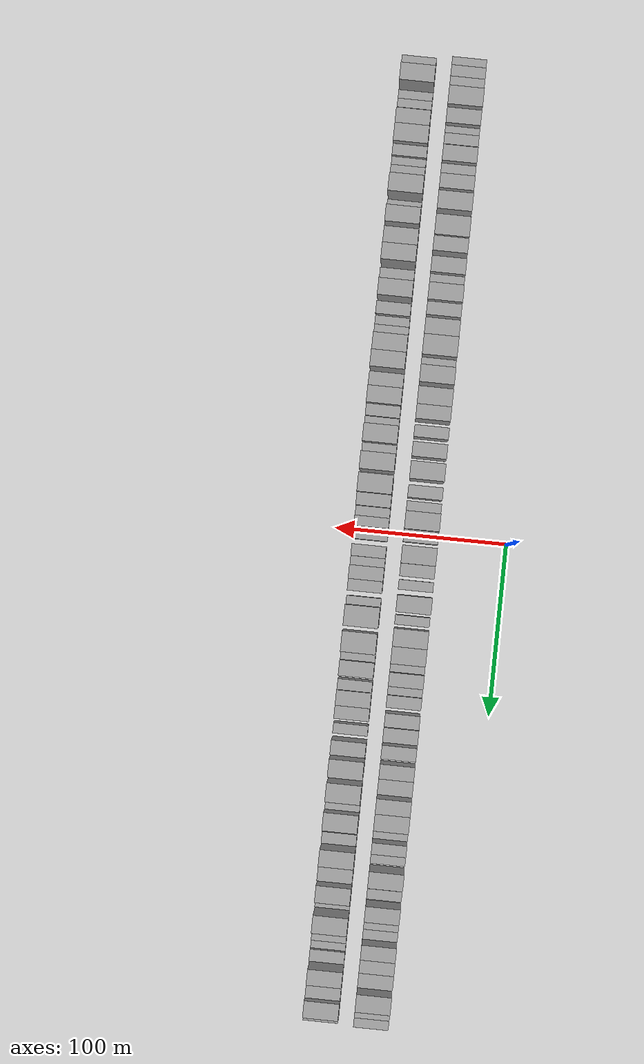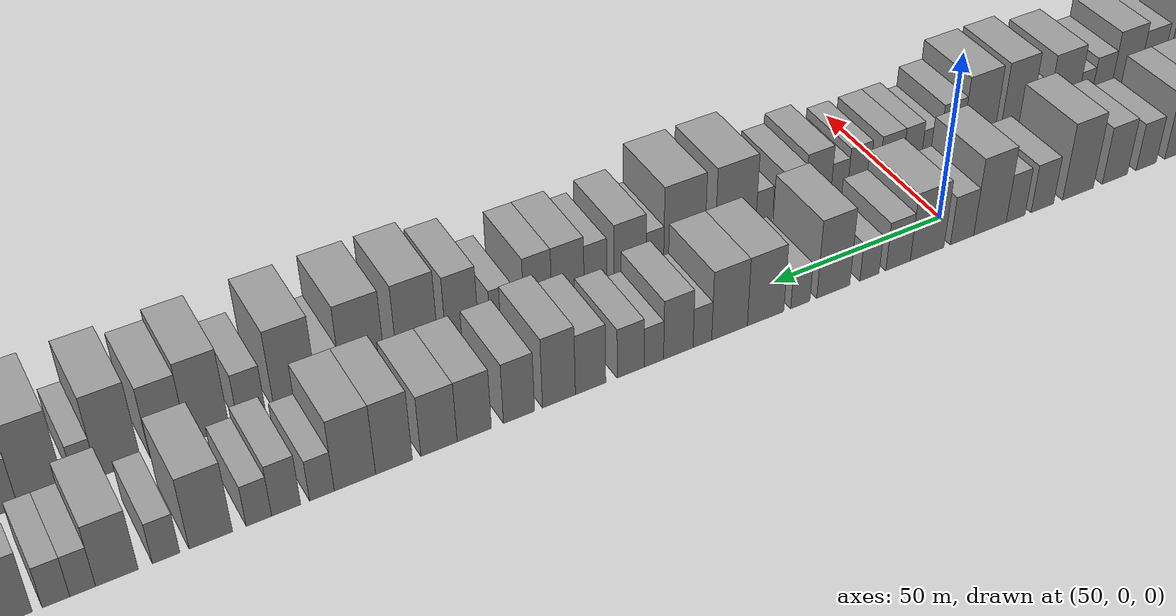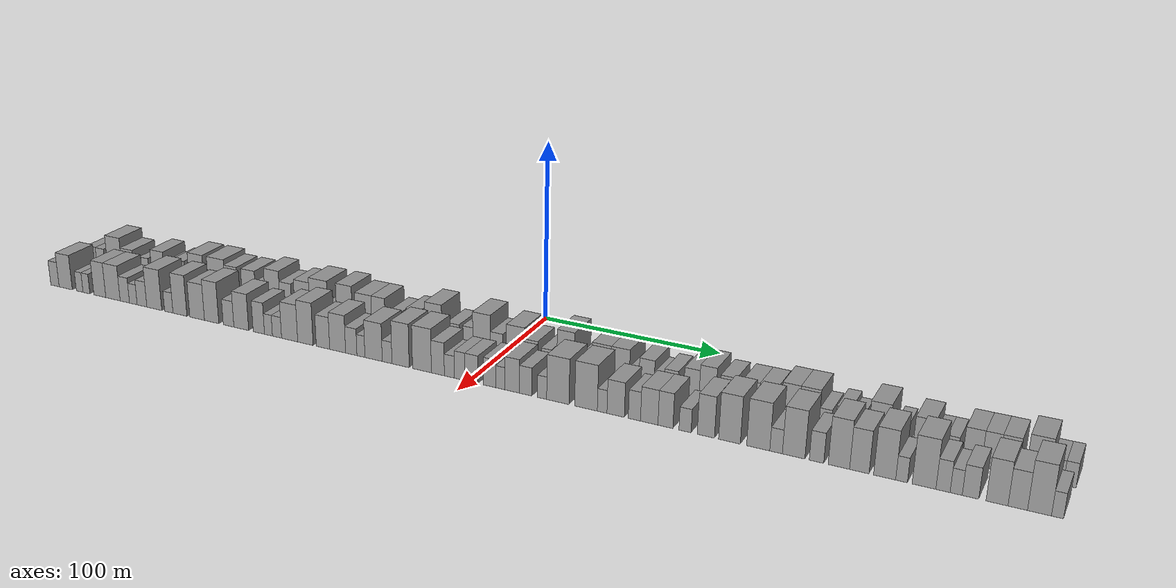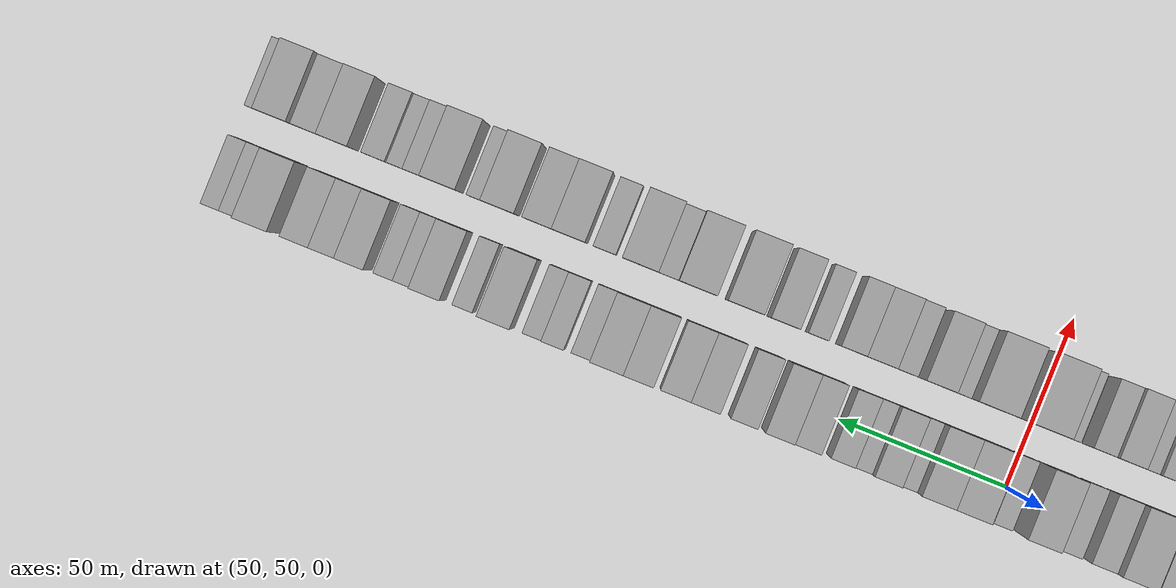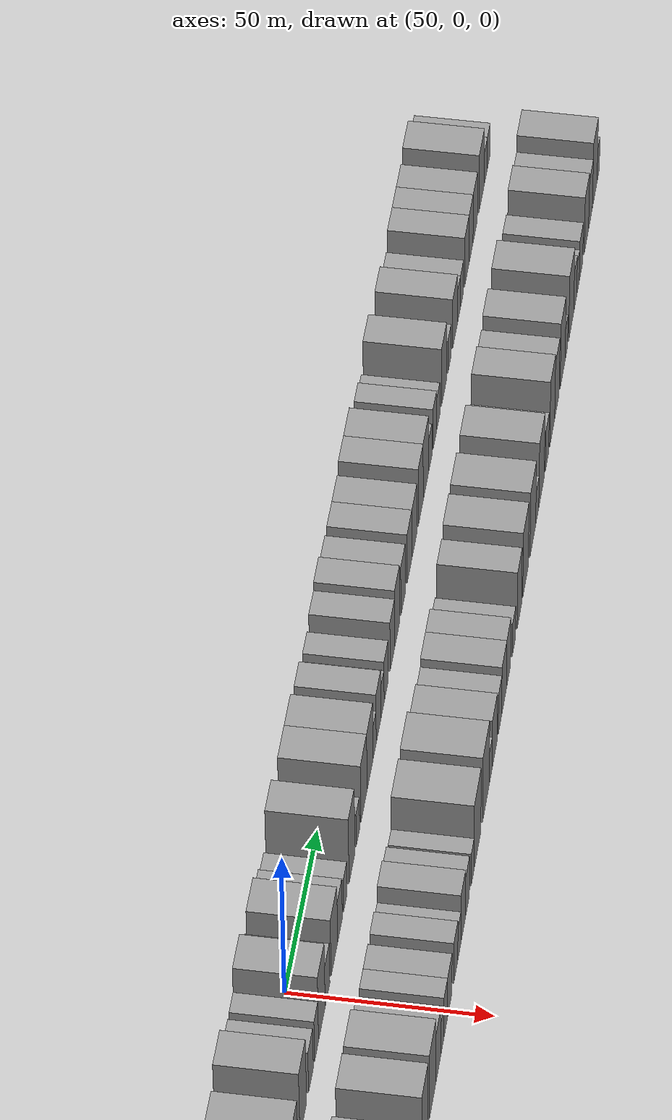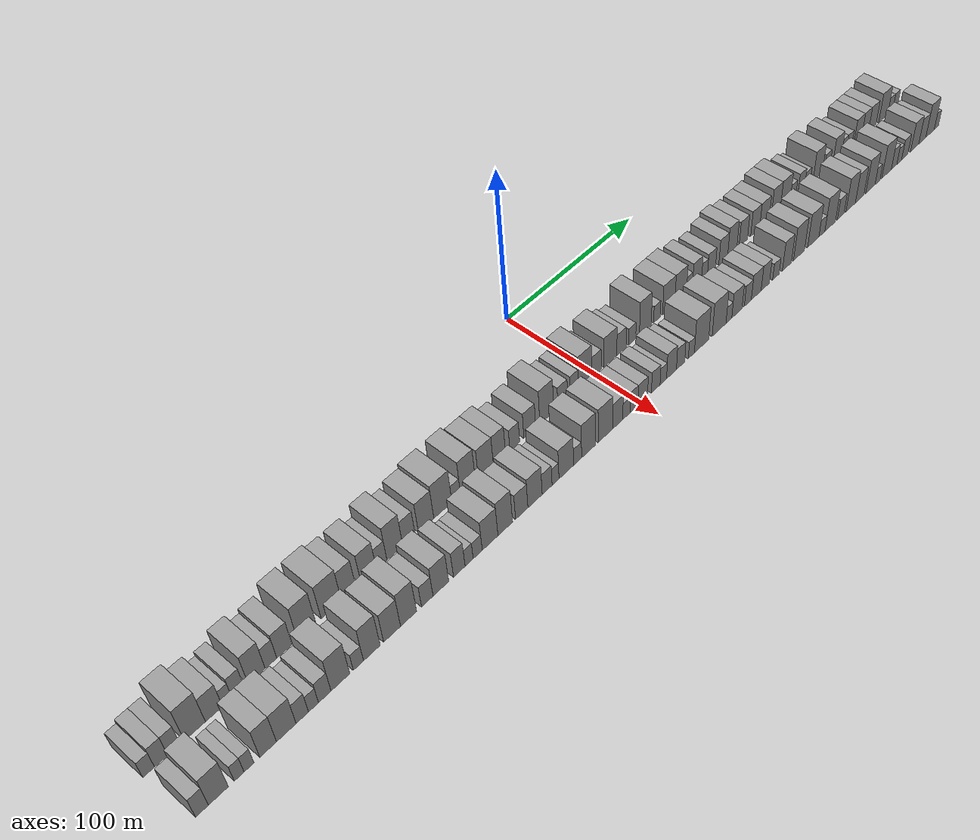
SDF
<sdf version="1.6">
 <world name="default">
  <scene>
   <sky><clouds><speed>12</speed></clouds></sky>
   <ambient>0.4 0.4 0.4 1</ambient>
   <background>0.7 0.7 0.7 1</background>
   <shadows>1</shadows>
  </scene>
  <gravity>0 0 -9.8066</gravity>
  <magnetic_field>6e-06 2.3e-05 -4.2e-05</magnetic_field>
  <physics default="0" name="default_physics" type="ode">
   <ode>
    <solver>
     <type>quick</type>
     <iters>10</iters>
     <sor>1.0</sor>
     <use_dynamic_moi_rescaling>0</use_dynamic_moi_rescaling>
    </solver>
    <constraints>
     <cfm>0</cfm>
     <erp>0.2</erp>
     <contact_max_correcting_vel>100</contact_max_correcting_vel>
     <contact_surface_layer>0.001</contact_surface_layer>
    </constraints>
   </ode>
   <max_step_size>0.004</max_step_size>
   <real_time_factor>1</real_time_factor>
   <real_time_update_rate>250</real_time_update_rate>
  </physics>
  <light name="sun" type="directional">
   <pose>0 0 10 0 0 0</pose>
   <diffuse>0.8 0.8 0.8 1</diffuse>
   <specular>0.2 0.2 0.2 1</specular>
   <attenuation>
    <range>1000</range>
    <constant>0.9</constant>
    <linear>0.01</linear>
    <quadratic>0.001</quadratic>
   </attenuation>
   <direction>-0.5 0.1 -0.9</direction>
  </light>
  <model name="building_1">
   <static>1</static>
   <pose>50.0000 -275.1089 0 0.000000 0.000000 0.000000</pose>
   <link name="link">
    <pose>0 0 6.00 0 0 0</pose>
    <collision name="collision"><geometry><box><size>20.0000 5.7822 12.0000</size></box></geometry></collision>
    <visual name="visual">
     <cast_shadows>0</cast_shadows>
     <geometry><box><size>20.0000 5.7822 12.0000</size></box></geometry>
     <material>
      <script>
       <uri>model://grey_wall/materials/scripts</uri>
       <uri>model://grey_wall/materials/textures</uri>
       <name>vrc/grey_wall</name>
      </script>
     </material>
    </visual>
   </link>
  </model>
  <model name="building_2">
   <static>1</static>
   <pose>50.0000 -268.9295 0 0.000000 0.000000 0.000000</pose>
   <link name="link">
    <pose>0 0 7.50 0 0 0</pose>
    <collision name="collision"><geometry><box><size>20.0000 6.5766 15.0000</size></box></geometry></collision>
    <visual name="visual">
     <cast_shadows>0</cast_shadows>
     <geometry><box><size>20.0000 6.5766 15.0000</size></box></geometry>
     <material>
      <script>
       <uri>model://grey_wall/materials/scripts</uri>
       <uri>model://grey_wall/materials/textures</uri>
       <name>vrc/grey_wall</name>
      </script>
     </material>
    </visual>
   </link>
  </model>
  <model name="building_3">
   <static>1</static>
   <pose>50.0000 -262.5161 0 0.000000 0.000000 0.000000</pose>
   <link name="link">
    <pose>0 0 7.50 0 0 0</pose>
    <collision name="collision"><geometry><box><size>20.0000 6.2501 15.0000</size></box></geometry></collision>
    <visual name="visual">
     <cast_shadows>0</cast_shadows>
     <geometry><box><size>20.0000 6.2501 15.0000</size></box></geometry>
     <material>
      <script>
       <uri>model://grey_wall/materials/scripts</uri>
       <uri>model://grey_wall/materials/textures</uri>
       <name>vrc/grey_wall</name>
      </script>
     </material>
    </visual>
   </link>
  </model>
  <model name="building_4">
   <static>1</static>
   <pose>50.0000 -251.9828 0 0.000000 0.000000 0.000000</pose>
   <link name="link">
    <pose>0 0 12.00 0 0 0</pose>
    <collision name="collision"><geometry><box><size>20.0000 10.8165 24.0000</size></box></geometry></collision>
    <visual name="visual">
     <cast_shadows>0</cast_shadows>
     <geometry><box><size>20.0000 10.8165 24.0000</size></box></geometry>
     <material>
      <script>
       <uri>model://grey_wall/materials/scripts</uri>
       <uri>model://grey_wall/materials/textures</uri>
       <name>vrc/grey_wall</name>
      </script>
     </material>
    </visual>
   </link>
  </model>
  <model name="building_5">
   <static>1</static>
   <pose>50.0000 -242.1096 0 0.000000 0.000000 0.000000</pose>
   <link name="link">
    <pose>0 0 9.00 0 0 0</pose>
    <collision name="collision"><geometry><box><size>20.0000 8.9300 18.0000</size></box></geometry></collision>
    <visual name="visual">
     <cast_shadows>0</cast_shadows>
     <geometry><box><size>20.0000 8.9300 18.0000</size></box></geometry>
     <material>
      <script>
       <uri>model://grey_wall/materials/scripts</uri>
       <uri>model://grey_wall/materials/textures</uri>
       <name>vrc/grey_wall</name>
      </script>
     </material>
    </visual>
   </link>
  </model>
  <model name="building_6">
   <static>1</static>
   <pose>50.0000 -235.1365 0 0.000000 0.000000 0.000000</pose>
   <link name="link">
    <pose>0 0 6.00 0 0 0</pose>
    <collision name="collision"><geometry><box><size>20.0000 5.0162 12.0000</size></box></geometry></collision>
    <visual name="visual">
     <cast_shadows>0</cast_shadows>
     <geometry><box><size>20.0000 5.0162 12.0000</size></box></geometry>
     <material>
      <script>
       <uri>model://grey_wall/materials/scripts</uri>
       <uri>model://grey_wall/materials/textures</uri>
       <name>vrc/grey_wall</name>
      </script>
     </material>
    </visual>
   </link>
  </model>
  <model name="building_7">
   <static>1</static>
   <pose>50.0000 -229.3773 0 0.000000 0.000000 0.000000</pose>
   <link name="link">
    <pose>0 0 7.50 0 0 0</pose>
    <collision name="collision"><geometry><box><size>20.0000 6.5023 15.0000</size></box></geometry></collision>
    <visual name="visual">
     <cast_shadows>0</cast_shadows>
     <geometry><box><size>20.0000 6.5023 15.0000</size></box></geometry>
     <material>
      <script>
       <uri>model://grey_wall/materials/scripts</uri>
       <uri>model://grey_wall/materials/textures</uri>
       <name>vrc/grey_wall</name>
      </script>
     </material>
    </visual>
   </link>
  </model>
  <model name="building_8">
   <static>1</static>
   <pose>50.0000 -219.4971 0 0.000000 0.000000 0.000000</pose>
   <link name="link">
    <pose>0 0 10.50 0 0 0</pose>
    <collision name="collision"><geometry><box><size>20.0000 9.2581 21.0000</size></box></geometry></collision>
    <visual name="visual">
     <cast_shadows>0</cast_shadows>
     <geometry><box><size>20.0000 9.2581 21.0000</size></box></geometry>
     <material>
      <script>
       <uri>model://grey_wall/materials/scripts</uri>
       <uri>model://grey_wall/materials/textures</uri>
       <name>vrc/grey_wall</name>
      </script>
     </material>
    </visual>
   </link>
  </model>
  <model name="building_9">
   <static>1</static>
   <pose>50.0000 -211.6525 0 0.000000 0.000000 0.000000</pose>
   <link name="link">
    <pose>0 0 7.50 0 0 0</pose>
    <collision name="collision"><geometry><box><size>20.0000 6.4310 15.0000</size></box></geometry></collision>
    <visual name="visual">
     <cast_shadows>0</cast_shadows>
     <geometry><box><size>20.0000 6.4310 15.0000</size></box></geometry>
     <material>
      <script>
       <uri>model://grey_wall/materials/scripts</uri>
       <uri>model://grey_wall/materials/textures</uri>
       <name>vrc/grey_wall</name>
      </script>
     </material>
    </visual>
   </link>
  </model>
  <model name="building_10">
   <static>1</static>
   <pose>50.0000 -204.1754 0 0.000000 0.000000 0.000000</pose>
   <link name="link">
    <pose>0 0 9.00 0 0 0</pose>
    <collision name="collision"><geometry><box><size>20.0000 8.5232 18.0000</size></box></geometry></collision>
    <visual name="visual">
     <cast_shadows>0</cast_shadows>
     <geometry><box><size>20.0000 8.5232 18.0000</size></box></geometry>
     <material>
      <script>
       <uri>model://grey_wall/materials/scripts</uri>
       <uri>model://grey_wall/materials/textures</uri>
       <name>vrc/grey_wall</name>
      </script>
     </material>
    </visual>
   </link>
  </model>
  <model name="building_11">
   <static>1</static>
   <pose>50.0000 -191.6460 0 0.000000 0.000000 0.000000</pose>
   <link name="link">
    <pose>0 0 12.00 0 0 0</pose>
    <collision name="collision"><geometry><box><size>20.0000 10.5356 24.0000</size></box></geometry></collision>
    <visual name="visual">
     <cast_shadows>0</cast_shadows>
     <geometry><box><size>20.0000 10.5356 24.0000</size></box></geometry>
     <material>
      <script>
       <uri>model://grey_wall/materials/scripts</uri>
       <uri>model://grey_wall/materials/textures</uri>
       <name>vrc/grey_wall</name>
      </script>
     </material>
    </visual>
   </link>
  </model>
  <model name="building_12">
   <static>1</static>
   <pose>50.0000 -177.4696 0 0.000000 0.000000 0.000000</pose>
   <link name="link">
    <pose>0 0 12.00 0 0 0</pose>
    <collision name="collision"><geometry><box><size>20.0000 11.8173 24.0000</size></box></geometry></collision>
    <visual name="visual">
     <cast_shadows>0</cast_shadows>
     <geometry><box><size>20.0000 11.8173 24.0000</size></box></geometry>
     <material>
      <script>
       <uri>model://grey_wall/materials/scripts</uri>
       <uri>model://grey_wall/materials/textures</uri>
       <name>vrc/grey_wall</name>
      </script>
     </material>
    </visual>
   </link>
  </model>
  <model name="building_13">
   <static>1</static>
   <pose>50.0000 -167.2322 0 0.000000 0.000000 0.000000</pose>
   <link name="link">
    <pose>0 0 10.50 0 0 0</pose>
    <collision name="collision"><geometry><box><size>20.0000 8.6574 21.0000</size></box></geometry></collision>
    <visual name="visual">
     <cast_shadows>0</cast_shadows>
     <geometry><box><size>20.0000 8.6574 21.0000</size></box></geometry>
     <material>
      <script>
       <uri>model://grey_wall/materials/scripts</uri>
       <uri>model://grey_wall/materials/textures</uri>
       <name>vrc/grey_wall</name>
      </script>
     </material>
    </visual>
   </link>
  </model>
  <model name="building_14">
   <static>1</static>
   <pose>50.0000 -155.2473 0 0.000000 0.000000 0.000000</pose>
   <link name="link">
    <pose>0 0 10.50 0 0 0</pose>
    <collision name="collision"><geometry><box><size>20.0000 9.3124 21.0000</size></box></geometry></collision>
    <visual name="visual">
     <cast_shadows>0</cast_shadows>
     <geometry><box><size>20.0000 9.3124 21.0000</size></box></geometry>
     <material>
      <script>
       <uri>model://grey_wall/materials/scripts</uri>
       <uri>model://grey_wall/materials/textures</uri>
       <name>vrc/grey_wall</name>
      </script>
     </material>
    </visual>
   </link>
  </model>
  <model name="building_15">
   <static>1</static>
   <pose>50.0000 -147.3577 0 0.000000 0.000000 0.000000</pose>
   <link name="link">
    <pose>0 0 7.50 0 0 0</pose>
    <collision name="collision"><geometry><box><size>20.0000 6.4668 15.0000</size></box></geometry></collision>
    <visual name="visual">
     <cast_shadows>0</cast_shadows>
     <geometry><box><size>20.0000 6.4668 15.0000</size></box></geometry>
     <material>
      <script>
       <uri>model://grey_wall/materials/scripts</uri>
       <uri>model://grey_wall/materials/textures</uri>
       <name>vrc/grey_wall</name>
      </script>
     </material>
    </visual>
   </link>
  </model>
  <model name="building_16">
   <static>1</static>
   <pose>50.0000 -139.1707 0 0.000000 0.000000 0.000000</pose>
   <link name="link">
    <pose>0 0 12.00 0 0 0</pose>
    <collision name="collision"><geometry><box><size>20.0000 9.9072 24.0000</size></box></geometry></collision>
    <visual name="visual">
     <cast_shadows>0</cast_shadows>
     <geometry><box><size>20.0000 9.9072 24.0000</size></box></geometry>
     <material>
      <script>
       <uri>model://grey_wall/materials/scripts</uri>
       <uri>model://grey_wall/materials/textures</uri>
       <name>vrc/grey_wall</name>
      </script>
     </material>
    </visual>
   </link>
  </model>
  <model name="building_17">
   <static>1</static>
   <pose>50.0000 -130.3272 0 0.000000 0.000000 0.000000</pose>
   <link name="link">
    <pose>0 0 9.00 0 0 0</pose>
    <collision name="collision"><geometry><box><size>20.0000 7.7798 18.0000</size></box></geometry></collision>
    <visual name="visual">
     <cast_shadows>0</cast_shadows>
     <geometry><box><size>20.0000 7.7798 18.0000</size></box></geometry>
     <material>
      <script>
       <uri>model://grey_wall/materials/scripts</uri>
       <uri>model://grey_wall/materials/textures</uri>
       <name>vrc/grey_wall</name>
      </script>
     </material>
    </visual>
   </link>
  </model>
  <model name="building_18">
   <static>1</static>
   <pose>50.0000 -119.4666 0 0.000000 0.000000 0.000000</pose>
   <link name="link">
    <pose>0 0 10.50 0 0 0</pose>
    <collision name="collision"><geometry><box><size>20.0000 9.9414 21.0000</size></box></geometry></collision>
    <visual name="visual">
     <cast_shadows>0</cast_shadows>
     <geometry><box><size>20.0000 9.9414 21.0000</size></box></geometry>
     <material>
      <script>
       <uri>model://grey_wall/materials/scripts</uri>
       <uri>model://grey_wall/materials/textures</uri>
       <name>vrc/grey_wall</name>
      </script>
     </material>
    </visual>
   </link>
  </model>
  <model name="building_19">
   <static>1</static>
   <pose>50.0000 -108.5932 0 0.000000 0.000000 0.000000</pose>
   <link name="link">
    <pose>0 0 12.00 0 0 0</pose>
    <collision name="collision"><geometry><box><size>20.0000 11.8054 24.0000</size></box></geometry></collision>
    <visual name="visual">
     <cast_shadows>0</cast_shadows>
     <geometry><box><size>20.0000 11.8054 24.0000</size></box></geometry>
     <material>
      <script>
       <uri>model://grey_wall/materials/scripts</uri>
       <uri>model://grey_wall/materials/textures</uri>
       <name>vrc/grey_wall</name>
      </script>
     </material>
    </visual>
   </link>
  </model>
  <model name="building_20">
   <static>1</static>
   <pose>50.0000 -99.8213 0 0.000000 0.000000 0.000000</pose>
   <link name="link">
    <pose>0 0 6.00 0 0 0</pose>
    <collision name="collision"><geometry><box><size>20.0000 5.7384 12.0000</size></box></geometry></collision>
    <visual name="visual">
     <cast_shadows>0</cast_shadows>
     <geometry><box><size>20.0000 5.7384 12.0000</size></box></geometry>
     <material>
      <script>
       <uri>model://grey_wall/materials/scripts</uri>
       <uri>model://grey_wall/materials/textures</uri>
       <name>vrc/grey_wall</name>
      </script>
     </material>
    </visual>
   </link>
  </model>
  <model name="building_21">
   <static>1</static>
   <pose>50.0000 -91.9319 0 0.000000 0.000000 0.000000</pose>
   <link name="link">
    <pose>0 0 12.00 0 0 0</pose>
    <collision name="collision"><geometry><box><size>20.0000 10.0403 24.0000</size></box></geometry></collision>
    <visual name="visual">
     <cast_shadows>0</cast_shadows>
     <geometry><box><size>20.0000 10.0403 24.0000</size></box></geometry>
     <material>
      <script>
       <uri>model://grey_wall/materials/scripts</uri>
       <uri>model://grey_wall/materials/textures</uri>
       <name>vrc/grey_wall</name>
      </script>
     </material>
    </visual>
   </link>
  </model>
  <model name="building_22">
   <static>1</static>
   <pose>50.0000 -79.7915 0 0.000000 0.000000 0.000000</pose>
   <link name="link">
    <pose>0 0 10.50 0 0 0</pose>
    <collision name="collision"><geometry><box><size>20.0000 10.2406 21.0000</size></box></geometry></collision>
    <visual name="visual">
     <cast_shadows>0</cast_shadows>
     <geometry><box><size>20.0000 10.2406 21.0000</size></box></geometry>
     <material>
      <script>
       <uri>model://grey_wall/materials/scripts</uri>
       <uri>model://grey_wall/materials/textures</uri>
       <name>vrc/grey_wall</name>
      </script>
     </material>
    </visual>
   </link>
  </model>
  <model name="building_23">
   <static>1</static>
   <pose>50.0000 -70.4306 0 0.000000 0.000000 0.000000</pose>
   <link name="link">
    <pose>0 0 10.50 0 0 0</pose>
    <collision name="collision"><geometry><box><size>20.0000 8.4810 21.0000</size></box></geometry></collision>
    <visual name="visual">
     <cast_shadows>0</cast_shadows>
     <geometry><box><size>20.0000 8.4810 21.0000</size></box></geometry>
     <material>
      <script>
       <uri>model://grey_wall/materials/scripts</uri>
       <uri>model://grey_wall/materials/textures</uri>
       <name>vrc/grey_wall</name>
      </script>
     </material>
    </visual>
   </link>
  </model>
  <model name="building_24">
   <static>1</static>
   <pose>50.0000 -59.7306 0 0.000000 0.000000 0.000000</pose>
   <link name="link">
    <pose>0 0 7.50 0 0 0</pose>
    <collision name="collision"><geometry><box><size>20.0000 6.9190 15.0000</size></box></geometry></collision>
    <visual name="visual">
     <cast_shadows>0</cast_shadows>
     <geometry><box><size>20.0000 6.9190 15.0000</size></box></geometry>
     <material>
      <script>
       <uri>model://grey_wall/materials/scripts</uri>
       <uri>model://grey_wall/materials/textures</uri>
       <name>vrc/grey_wall</name>
      </script>
     </material>
    </visual>
   </link>
  </model>
  <model name="building_25">
   <static>1</static>
   <pose>50.0000 -49.0280 0 0.000000 0.000000 0.000000</pose>
   <link name="link">
    <pose>0 0 9.00 0 0 0</pose>
    <collision name="collision"><geometry><box><size>20.0000 8.4862 18.0000</size></box></geometry></collision>
    <visual name="visual">
     <cast_shadows>0</cast_shadows>
     <geometry><box><size>20.0000 8.4862 18.0000</size></box></geometry>
     <material>
      <script>
       <uri>model://grey_wall/materials/scripts</uri>
       <uri>model://grey_wall/materials/textures</uri>
       <name>vrc/grey_wall</name>
      </script>
     </material>
    </visual>
   </link>
  </model>
  <model name="building_26">
   <static>1</static>
   <pose>50.0000 -36.6869 0 0.000000 0.000000 0.000000</pose>
   <link name="link">
    <pose>0 0 12.00 0 0 0</pose>
    <collision name="collision"><geometry><box><size>20.0000 10.1959 24.0000</size></box></geometry></collision>
    <visual name="visual">
     <cast_shadows>0</cast_shadows>
     <geometry><box><size>20.0000 10.1959 24.0000</size></box></geometry>
     <material>
      <script>
       <uri>model://grey_wall/materials/scripts</uri>
       <uri>model://grey_wall/materials/textures</uri>
       <name>vrc/grey_wall</name>
      </script>
     </material>
    </visual>
   </link>
  </model>
  <model name="building_27">
   <static>1</static>
   <pose>50.0000 -24.9346 0 0.000000 0.000000 0.000000</pose>
   <link name="link">
    <pose>0 0 7.50 0 0 0</pose>
    <collision name="collision"><geometry><box><size>20.0000 7.3088 15.0000</size></box></geometry></collision>
    <visual name="visual">
     <cast_shadows>0</cast_shadows>
     <geometry><box><size>20.0000 7.3088 15.0000</size></box></geometry>
     <material>
      <script>
       <uri>model://grey_wall/materials/scripts</uri>
       <uri>model://grey_wall/materials/textures</uri>
       <name>vrc/grey_wall</name>
      </script>
     </material>
    </visual>
   </link>
  </model>
  <model name="building_28">
   <static>1</static>
   <pose>50.0000 -16.2581 0 0.000000 0.000000 0.000000</pose>
   <link name="link">
    <pose>0 0 7.50 0 0 0</pose>
    <collision name="collision"><geometry><box><size>20.0000 6.0442 15.0000</size></box></geometry></collision>
    <visual name="visual">
     <cast_shadows>0</cast_shadows>
     <geometry><box><size>20.0000 6.0442 15.0000</size></box></geometry>
     <material>
      <script>
       <uri>model://grey_wall/materials/scripts</uri>
       <uri>model://grey_wall/materials/textures</uri>
       <name>vrc/grey_wall</name>
      </script>
     </material>
    </visual>
   </link>
  </model>
  <model name="building_29">
   <static>1</static>
   <pose>50.0000 -8.1010 0 0.000000 0.000000 0.000000</pose>
   <link name="link">
    <pose>0 0 12.00 0 0 0</pose>
    <collision name="collision"><geometry><box><size>20.0000 10.2699 24.0000</size></box></geometry></collision>
    <visual name="visual">
     <cast_shadows>0</cast_shadows>
     <geometry><box><size>20.0000 10.2699 24.0000</size></box></geometry>
     <material>
      <script>
       <uri>model://grey_wall/materials/scripts</uri>
       <uri>model://grey_wall/materials/textures</uri>
       <name>vrc/grey_wall</name>
      </script>
     </material>
    </visual>
   </link>
  </model>
  <model name="building_30">
   <static>1</static>
   <pose>50.0000 0.6903 0 0.000000 0.000000 0.000000</pose>
   <link name="link">
    <pose>0 0 7.50 0 0 0</pose>
    <collision name="collision"><geometry><box><size>20.0000 7.3128 15.0000</size></box></geometry></collision>
    <visual name="visual">
     <cast_shadows>0</cast_shadows>
     <geometry><box><size>20.0000 7.3128 15.0000</size></box></geometry>
     <material>
      <script>
       <uri>model://grey_wall/materials/scripts</uri>
       <uri>model://grey_wall/materials/textures</uri>
       <name>vrc/grey_wall</name>
      </script>
     </material>
    </visual>
   </link>
  </model>
  <model name="building_31">
   <static>1</static>
   <pose>50.0000 11.5053 0 0.000000 0.000000 0.000000</pose>
   <link name="link">
    <pose>0 0 10.50 0 0 0</pose>
    <collision name="collision"><geometry><box><size>20.0000 10.3172 21.0000</size></box></geometry></collision>
    <visual name="visual">
     <cast_shadows>0</cast_shadows>
     <geometry><box><size>20.0000 10.3172 21.0000</size></box></geometry>
     <material>
      <script>
       <uri>model://grey_wall/materials/scripts</uri>
       <uri>model://grey_wall/materials/textures</uri>
       <name>vrc/grey_wall</name>
      </script>
     </material>
    </visual>
   </link>
  </model>
  <model name="building_32">
   <static>1</static>
   <pose>50.0000 20.3756 0 0.000000 0.000000 0.000000</pose>
   <link name="link">
    <pose>0 0 7.50 0 0 0</pose>
    <collision name="collision"><geometry><box><size>20.0000 7.4232 15.0000</size></box></geometry></collision>
    <visual name="visual">
     <cast_shadows>0</cast_shadows>
     <geometry><box><size>20.0000 7.4232 15.0000</size></box></geometry>
     <material>
      <script>
       <uri>model://grey_wall/materials/scripts</uri>
       <uri>model://grey_wall/materials/textures</uri>
       <name>vrc/grey_wall</name>
      </script>
     </material>
    </visual>
   </link>
  </model>
  <model name="building_33">
   <static>1</static>
   <pose>50.0000 28.9492 0 0.000000 0.000000 0.000000</pose>
   <link name="link">
    <pose>0 0 6.00 0 0 0</pose>
    <collision name="collision"><geometry><box><size>20.0000 5.7240 12.0000</size></box></geometry></collision>
    <visual name="visual">
     <cast_shadows>0</cast_shadows>
     <geometry><box><size>20.0000 5.7240 12.0000</size></box></geometry>
     <material>
      <script>
       <uri>model://grey_wall/materials/scripts</uri>
       <uri>model://grey_wall/materials/textures</uri>
       <name>vrc/grey_wall</name>
      </script>
     </material>
    </visual>
   </link>
  </model>
  <model name="building_34">
   <static>1</static>
   <pose>50.0000 39.6320 0 0.000000 0.000000 0.000000</pose>
   <link name="link">
    <pose>0 0 12.00 0 0 0</pose>
    <collision name="collision"><geometry><box><size>20.0000 9.6415 24.0000</size></box></geometry></collision>
    <visual name="visual">
     <cast_shadows>0</cast_shadows>
     <geometry><box><size>20.0000 9.6415 24.0000</size></box></geometry>
     <material>
      <script>
       <uri>model://grey_wall/materials/scripts</uri>
       <uri>model://grey_wall/materials/textures</uri>
       <name>vrc/grey_wall</name>
      </script>
     </material>
    </visual>
   </link>
  </model>
  <model name="building_35">
   <static>1</static>
   <pose>50.0000 49.2087 0 0.000000 0.000000 0.000000</pose>
   <link name="link">
    <pose>0 0 6.00 0 0 0</pose>
    <collision name="collision"><geometry><box><size>20.0000 5.5118 12.0000</size></box></geometry></collision>
    <visual name="visual">
     <cast_shadows>0</cast_shadows>
     <geometry><box><size>20.0000 5.5118 12.0000</size></box></geometry>
     <material>
      <script>
       <uri>model://grey_wall/materials/scripts</uri>
       <uri>model://grey_wall/materials/textures</uri>
       <name>vrc/grey_wall</name>
      </script>
     </material>
    </visual>
   </link>
  </model>
  <model name="building_36">
   <static>1</static>
   <pose>50.0000 59.1062 0 0.000000 0.000000 0.000000</pose>
   <link name="link">
    <pose>0 0 10.50 0 0 0</pose>
    <collision name="collision"><geometry><box><size>20.0000 10.2832 21.0000</size></box></geometry></collision>
    <visual name="visual">
     <cast_shadows>0</cast_shadows>
     <geometry><box><size>20.0000 10.2832 21.0000</size></box></geometry>
     <material>
      <script>
       <uri>model://grey_wall/materials/scripts</uri>
       <uri>model://grey_wall/materials/textures</uri>
       <name>vrc/grey_wall</name>
      </script>
     </material>
    </visual>
   </link>
  </model>
  <model name="building_37">
   <static>1</static>
   <pose>50.0000 69.2046 0 0.000000 0.000000 0.000000</pose>
   <link name="link">
    <pose>0 0 10.50 0 0 0</pose>
    <collision name="collision"><geometry><box><size>20.0000 9.9137 21.0000</size></box></geometry></collision>
    <visual name="visual">
     <cast_shadows>0</cast_shadows>
     <geometry><box><size>20.0000 9.9137 21.0000</size></box></geometry>
     <material>
      <script>
       <uri>model://grey_wall/materials/scripts</uri>
       <uri>model://grey_wall/materials/textures</uri>
       <name>vrc/grey_wall</name>
      </script>
     </material>
    </visual>
   </link>
  </model>
  <model name="building_38">
   <static>1</static>
   <pose>50.0000 76.7131 0 0.000000 0.000000 0.000000</pose>
   <link name="link">
    <pose>0 0 6.00 0 0 0</pose>
    <collision name="collision"><geometry><box><size>20.0000 5.1032 12.0000</size></box></geometry></collision>
    <visual name="visual">
     <cast_shadows>0</cast_shadows>
     <geometry><box><size>20.0000 5.1032 12.0000</size></box></geometry>
     <material>
      <script>
       <uri>model://grey_wall/materials/scripts</uri>
       <uri>model://grey_wall/materials/textures</uri>
       <name>vrc/grey_wall</name>
      </script>
     </material>
    </visual>
   </link>
  </model>
  <model name="building_39">
   <static>1</static>
   <pose>50.0000 83.2646 0 0.000000 0.000000 0.000000</pose>
   <link name="link">
    <pose>0 0 9.00 0 0 0</pose>
    <collision name="collision"><geometry><box><size>20.0000 7.9998 18.0000</size></box></geometry></collision>
    <visual name="visual">
     <cast_shadows>0</cast_shadows>
     <geometry><box><size>20.0000 7.9998 18.0000</size></box></geometry>
     <material>
      <script>
       <uri>model://grey_wall/materials/scripts</uri>
       <uri>model://grey_wall/materials/textures</uri>
       <name>vrc/grey_wall</name>
      </script>
     </material>
    </visual>
   </link>
  </model>
  <model name="building_40">
   <static>1</static>
   <pose>50.0000 89.8730 0 0.000000 0.000000 0.000000</pose>
   <link name="link">
    <pose>0 0 6.00 0 0 0</pose>
    <collision name="collision"><geometry><box><size>20.0000 5.2170 12.0000</size></box></geometry></collision>
    <visual name="visual">
     <cast_shadows>0</cast_shadows>
     <geometry><box><size>20.0000 5.2170 12.0000</size></box></geometry>
     <material>
      <script>
       <uri>model://grey_wall/materials/scripts</uri>
       <uri>model://grey_wall/materials/textures</uri>
       <name>vrc/grey_wall</name>
      </script>
     </material>
    </visual>
   </link>
  </model>
  <model name="building_41">
   <static>1</static>
   <pose>50.0000 96.0409 0 0.000000 0.000000 0.000000</pose>
   <link name="link">
    <pose>0 0 7.50 0 0 0</pose>
    <collision name="collision"><geometry><box><size>20.0000 7.1189 15.0000</size></box></geometry></collision>
    <visual name="visual">
     <cast_shadows>0</cast_shadows>
     <geometry><box><size>20.0000 7.1189 15.0000</size></box></geometry>
     <material>
      <script>
       <uri>model://grey_wall/materials/scripts</uri>
       <uri>model://grey_wall/materials/textures</uri>
       <name>vrc/grey_wall</name>
      </script>
     </material>
    </visual>
   </link>
  </model>
  <model name="building_42">
   <static>1</static>
   <pose>50.0000 106.5432 0 0.000000 0.000000 0.000000</pose>
   <link name="link">
    <pose>0 0 9.00 0 0 0</pose>
    <collision name="collision"><geometry><box><size>20.0000 7.8858 18.0000</size></box></geometry></collision>
    <visual name="visual">
     <cast_shadows>0</cast_shadows>
     <geometry><box><size>20.0000 7.8858 18.0000</size></box></geometry>
     <material>
      <script>
       <uri>model://grey_wall/materials/scripts</uri>
       <uri>model://grey_wall/materials/textures</uri>
       <name>vrc/grey_wall</name>
      </script>
     </material>
    </visual>
   </link>
  </model>
  <model name="building_43">
   <static>1</static>
   <pose>50.0000 114.6918 0 0.000000 0.000000 0.000000</pose>
   <link name="link">
    <pose>0 0 10.50 0 0 0</pose>
    <collision name="collision"><geometry><box><size>20.0000 8.4112 21.0000</size></box></geometry></collision>
    <visual name="visual">
     <cast_shadows>0</cast_shadows>
     <geometry><box><size>20.0000 8.4112 21.0000</size></box></geometry>
     <material>
      <script>
       <uri>model://grey_wall/materials/scripts</uri>
       <uri>model://grey_wall/materials/textures</uri>
       <name>vrc/grey_wall</name>
      </script>
     </material>
    </visual>
   </link>
  </model>
  <model name="building_44">
   <static>1</static>
   <pose>50.0000 124.8040 0 0.000000 0.000000 0.000000</pose>
   <link name="link">
    <pose>0 0 9.00 0 0 0</pose>
    <collision name="collision"><geometry><box><size>20.0000 7.8133 18.0000</size></box></geometry></collision>
    <visual name="visual">
     <cast_shadows>0</cast_shadows>
     <geometry><box><size>20.0000 7.8133 18.0000</size></box></geometry>
     <material>
      <script>
       <uri>model://grey_wall/materials/scripts</uri>
       <uri>model://grey_wall/materials/textures</uri>
       <name>vrc/grey_wall</name>
      </script>
     </material>
    </visual>
   </link>
  </model>
  <model name="building_45">
   <static>1</static>
   <pose>50.0000 135.9199 0 0.000000 0.000000 0.000000</pose>
   <link name="link">
    <pose>0 0 9.00 0 0 0</pose>
    <collision name="collision"><geometry><box><size>20.0000 8.4184 18.0000</size></box></geometry></collision>
    <visual name="visual">
     <cast_shadows>0</cast_shadows>
     <geometry><box><size>20.0000 8.4184 18.0000</size></box></geometry>
     <material>
      <script>
       <uri>model://grey_wall/materials/scripts</uri>
       <uri>model://grey_wall/materials/textures</uri>
       <name>vrc/grey_wall</name>
      </script>
     </material>
    </visual>
   </link>
  </model>
  <model name="building_46">
   <static>1</static>
   <pose>50.0000 144.5403 0 0.000000 0.000000 0.000000</pose>
   <link name="link">
    <pose>0 0 9.00 0 0 0</pose>
    <collision name="collision"><geometry><box><size>20.0000 8.8225 18.0000</size></box></geometry></collision>
    <visual name="visual">
     <cast_shadows>0</cast_shadows>
     <geometry><box><size>20.0000 8.8225 18.0000</size></box></geometry>
     <material>
      <script>
       <uri>model://grey_wall/materials/scripts</uri>
       <uri>model://grey_wall/materials/textures</uri>
       <name>vrc/grey_wall</name>
      </script>
     </material>
    </visual>
   </link>
  </model>
  <model name="building_47">
   <static>1</static>
   <pose>50.0000 155.3123 0 0.000000 0.000000 0.000000</pose>
   <link name="link">
    <pose>0 0 10.50 0 0 0</pose>
    <collision name="collision"><geometry><box><size>20.0000 8.7214 21.0000</size></box></geometry></collision>
    <visual name="visual">
     <cast_shadows>0</cast_shadows>
     <geometry><box><size>20.0000 8.7214 21.0000</size></box></geometry>
     <material>
      <script>
       <uri>model://grey_wall/materials/scripts</uri>
       <uri>model://grey_wall/materials/textures</uri>
       <name>vrc/grey_wall</name>
      </script>
     </material>
    </visual>
   </link>
  </model>
  <model name="building_48">
   <static>1</static>
   <pose>50.0000 164.4858 0 0.000000 0.000000 0.000000</pose>
   <link name="link">
    <pose>0 0 10.50 0 0 0</pose>
    <collision name="collision"><geometry><box><size>20.0000 9.6257 21.0000</size></box></geometry></collision>
    <visual name="visual">
     <cast_shadows>0</cast_shadows>
     <geometry><box><size>20.0000 9.6257 21.0000</size></box></geometry>
     <material>
      <script>
       <uri>model://grey_wall/materials/scripts</uri>
       <uri>model://grey_wall/materials/textures</uri>
       <name>vrc/grey_wall</name>
      </script>
     </material>
    </visual>
   </link>
  </model>
  <model name="building_49">
   <static>1</static>
   <pose>50.0000 172.1554 0 0.000000 0.000000 0.000000</pose>
   <link name="link">
    <pose>0 0 6.00 0 0 0</pose>
    <collision name="collision"><geometry><box><size>20.0000 5.7134 12.0000</size></box></geometry></collision>
    <visual name="visual">
     <cast_shadows>0</cast_shadows>
     <geometry><box><size>20.0000 5.7134 12.0000</size></box></geometry>
     <material>
      <script>
       <uri>model://grey_wall/materials/scripts</uri>
       <uri>model://grey_wall/materials/textures</uri>
       <name>vrc/grey_wall</name>
      </script>
     </material>
    </visual>
   </link>
  </model>
  <model name="building_50">
   <static>1</static>
   <pose>50.0000 180.2920 0 0.000000 0.000000 0.000000</pose>
   <link name="link">
    <pose>0 0 7.50 0 0 0</pose>
    <collision name="collision"><geometry><box><size>20.0000 6.5598 15.0000</size></box></geometry></collision>
    <visual name="visual">
     <cast_shadows>0</cast_shadows>
     <geometry><box><size>20.0000 6.5598 15.0000</size></box></geometry>
     <material>
      <script>
       <uri>model://grey_wall/materials/scripts</uri>
       <uri>model://grey_wall/materials/textures</uri>
       <name>vrc/grey_wall</name>
      </script>
     </material>
    </visual>
   </link>
  </model>
  <model name="building_51">
   <static>1</static>
   <pose>50.0000 186.4201 0 0.000000 0.000000 0.000000</pose>
   <link name="link">
    <pose>0 0 6.00 0 0 0</pose>
    <collision name="collision"><geometry><box><size>20.0000 5.6963 12.0000</size></box></geometry></collision>
    <visual name="visual">
     <cast_shadows>0</cast_shadows>
     <geometry><box><size>20.0000 5.6963 12.0000</size></box></geometry>
     <material>
      <script>
       <uri>model://grey_wall/materials/scripts</uri>
       <uri>model://grey_wall/materials/textures</uri>
       <name>vrc/grey_wall</name>
      </script>
     </material>
    </visual>
   </link>
  </model>
  <model name="building_52">
   <static>1</static>
   <pose>50.0000 197.0179 0 0.000000 0.000000 0.000000</pose>
   <link name="link">
    <pose>0 0 10.50 0 0 0</pose>
    <collision name="collision"><geometry><box><size>20.0000 9.4993 21.0000</size></box></geometry></collision>
    <visual name="visual">
     <cast_shadows>0</cast_shadows>
     <geometry><box><size>20.0000 9.4993 21.0000</size></box></geometry>
     <material>
      <script>
       <uri>model://grey_wall/materials/scripts</uri>
       <uri>model://grey_wall/materials/textures</uri>
       <name>vrc/grey_wall</name>
      </script>
     </material>
    </visual>
   </link>
  </model>
  <model name="building_53">
   <static>1</static>
   <pose>50.0000 206.7184 0 0.000000 0.000000 0.000000</pose>
   <link name="link">
    <pose>0 0 6.00 0 0 0</pose>
    <collision name="collision"><geometry><box><size>20.0000 5.9018 12.0000</size></box></geometry></collision>
    <visual name="visual">
     <cast_shadows>0</cast_shadows>
     <geometry><box><size>20.0000 5.9018 12.0000</size></box></geometry>
     <material>
      <script>
       <uri>model://grey_wall/materials/scripts</uri>
       <uri>model://grey_wall/materials/textures</uri>
       <name>vrc/grey_wall</name>
      </script>
     </material>
    </visual>
   </link>
  </model>
  <model name="building_54">
   <static>1</static>
   <pose>50.0000 217.1489 0 0.000000 0.000000 0.000000</pose>
   <link name="link">
    <pose>0 0 9.00 0 0 0</pose>
    <collision name="collision"><geometry><box><size>20.0000 8.9592 18.0000</size></box></geometry></collision>
    <visual name="visual">
     <cast_shadows>0</cast_shadows>
     <geometry><box><size>20.0000 8.9592 18.0000</size></box></geometry>
     <material>
      <script>
       <uri>model://grey_wall/materials/scripts</uri>
       <uri>model://grey_wall/materials/textures</uri>
       <name>vrc/grey_wall</name>
      </script>
     </material>
    </visual>
   </link>
  </model>
  <model name="building_55">
   <static>1</static>
   <pose>50.0000 224.3023 0 0.000000 0.000000 0.000000</pose>
   <link name="link">
    <pose>0 0 6.00 0 0 0</pose>
    <collision name="collision"><geometry><box><size>20.0000 5.3476 12.0000</size></box></geometry></collision>
    <visual name="visual">
     <cast_shadows>0</cast_shadows>
     <geometry><box><size>20.0000 5.3476 12.0000</size></box></geometry>
     <material>
      <script>
       <uri>model://grey_wall/materials/scripts</uri>
       <uri>model://grey_wall/materials/textures</uri>
       <name>vrc/grey_wall</name>
      </script>
     </material>
    </visual>
   </link>
  </model>
  <model name="building_56">
   <static>1</static>
   <pose>50.0000 229.8016 0 0.000000 0.000000 0.000000</pose>
   <link name="link">
    <pose>0 0 6.00 0 0 0</pose>
    <collision name="collision"><geometry><box><size>20.0000 5.6511 12.0000</size></box></geometry></collision>
    <visual name="visual">
     <cast_shadows>0</cast_shadows>
     <geometry><box><size>20.0000 5.6511 12.0000</size></box></geometry>
     <material>
      <script>
       <uri>model://grey_wall/materials/scripts</uri>
       <uri>model://grey_wall/materials/textures</uri>
       <name>vrc/grey_wall</name>
      </script>
     </material>
    </visual>
   </link>
  </model>
  <model name="building_57">
   <static>1</static>
   <pose>50.0000 238.8254 0 0.000000 0.000000 0.000000</pose>
   <link name="link">
    <pose>0 0 9.00 0 0 0</pose>
    <collision name="collision"><geometry><box><size>20.0000 8.3964 18.0000</size></box></geometry></collision>
    <visual name="visual">
     <cast_shadows>0</cast_shadows>
     <geometry><box><size>20.0000 8.3964 18.0000</size></box></geometry>
     <material>
      <script>
       <uri>model://grey_wall/materials/scripts</uri>
       <uri>model://grey_wall/materials/textures</uri>
       <name>vrc/grey_wall</name>
      </script>
     </material>
    </visual>
   </link>
  </model>
  <model name="building_58">
   <static>1</static>
   <pose>50.0000 246.7431 0 0.000000 0.000000 0.000000</pose>
   <link name="link">
    <pose>0 0 9.00 0 0 0</pose>
    <collision name="collision"><geometry><box><size>20.0000 7.4389 18.0000</size></box></geometry></collision>
    <visual name="visual">
     <cast_shadows>0</cast_shadows>
     <geometry><box><size>20.0000 7.4389 18.0000</size></box></geometry>
     <material>
      <script>
       <uri>model://grey_wall/materials/scripts</uri>
       <uri>model://grey_wall/materials/textures</uri>
       <name>vrc/grey_wall</name>
      </script>
     </material>
    </visual>
   </link>
  </model>
  <model name="building_59">
   <static>1</static>
   <pose>50.0000 254.5801 0 0.000000 0.000000 0.000000</pose>
   <link name="link">
    <pose>0 0 9.00 0 0 0</pose>
    <collision name="collision"><geometry><box><size>20.0000 8.2352 18.0000</size></box></geometry></collision>
    <visual name="visual">
     <cast_shadows>0</cast_shadows>
     <geometry><box><size>20.0000 8.2352 18.0000</size></box></geometry>
     <material>
      <script>
       <uri>model://grey_wall/materials/scripts</uri>
       <uri>model://grey_wall/materials/textures</uri>
       <name>vrc/grey_wall</name>
      </script>
     </material>
    </visual>
   </link>
  </model>
  <model name="building_60">
   <static>1</static>
   <pose>50.0000 266.7092 0 0.000000 0.000000 0.000000</pose>
   <link name="link">
    <pose>0 0 10.50 0 0 0</pose>
    <collision name="collision"><geometry><box><size>20.0000 10.0229 21.0000</size></box></geometry></collision>
    <visual name="visual">
     <cast_shadows>0</cast_shadows>
     <geometry><box><size>20.0000 10.0229 21.0000</size></box></geometry>
     <material>
      <script>
       <uri>model://grey_wall/materials/scripts</uri>
       <uri>model://grey_wall/materials/textures</uri>
       <name>vrc/grey_wall</name>
      </script>
     </material>
    </visual>
   </link>
  </model>
  <model name="building_61">
   <static>1</static>
   <pose>50.0000 274.6319 0 0.000000 0.000000 0.000000</pose>
   <link name="link">
    <pose>0 0 6.00 0 0 0</pose>
    <collision name="collision"><geometry><box><size>20.0000 5.8225 12.0000</size></box></geometry></collision>
    <visual name="visual">
     <cast_shadows>0</cast_shadows>
     <geometry><box><size>20.0000 5.8225 12.0000</size></box></geometry>
     <material>
      <script>
       <uri>model://grey_wall/materials/scripts</uri>
       <uri>model://grey_wall/materials/textures</uri>
       <name>vrc/grey_wall</name>
      </script>
     </material>
    </visual>
   </link>
  </model>
  <model name="building_62">
   <static>1</static>
   <pose>50.0000 280.2019 0 0.000000 0.000000 0.000000</pose>
   <link name="link">
    <pose>0 0 6.00 0 0 0</pose>
    <collision name="collision"><geometry><box><size>20.0000 5.3176 12.0000</size></box></geometry></collision>
    <visual name="visual">
     <cast_shadows>0</cast_shadows>
     <geometry><box><size>20.0000 5.3176 12.0000</size></box></geometry>
     <material>
      <script>
       <uri>model://grey_wall/materials/scripts</uri>
       <uri>model://grey_wall/materials/textures</uri>
       <name>vrc/grey_wall</name>
      </script>
     </material>
    </visual>
   </link>
  </model>
  <model name="building_63">
   <static>1</static>
   <pose>79.0000 -271.8355 0 0.000000 0.000000 0.000000</pose>
   <link name="link">
    <pose>0 0 7.50 0 0 0</pose>
    <collision name="collision"><geometry><box><size>20.0000 6.3289 15.0000</size></box></geometry></collision>
    <visual name="visual">
     <cast_shadows>0</cast_shadows>
     <geometry><box><size>20.0000 6.3289 15.0000</size></box></geometry>
     <material>
      <script>
       <uri>model://grey_wall/materials/scripts</uri>
       <uri>model://grey_wall/materials/textures</uri>
       <name>vrc/grey_wall</name>
      </script>
     </material>
    </visual>
   </link>
  </model>
  <model name="building_64">
   <static>1</static>
   <pose>79.0000 -263.6766 0 0.000000 0.000000 0.000000</pose>
   <link name="link">
    <pose>0 0 10.50 0 0 0</pose>
    <collision name="collision"><geometry><box><size>20.0000 9.9889 21.0000</size></box></geometry></collision>
    <visual name="visual">
     <cast_shadows>0</cast_shadows>
     <geometry><box><size>20.0000 9.9889 21.0000</size></box></geometry>
     <material>
      <script>
       <uri>model://grey_wall/materials/scripts</uri>
       <uri>model://grey_wall/materials/textures</uri>
       <name>vrc/grey_wall</name>
      </script>
     </material>
    </visual>
   </link>
  </model>
  <model name="building_65">
   <static>1</static>
   <pose>79.0000 -253.1827 0 0.000000 0.000000 0.000000</pose>
   <link name="link">
    <pose>0 0 6.00 0 0 0</pose>
    <collision name="collision"><geometry><box><size>20.0000 4.9988 12.0000</size></box></geometry></collision>
    <visual name="visual">
     <cast_shadows>0</cast_shadows>
     <geometry><box><size>20.0000 4.9988 12.0000</size></box></geometry>
     <material>
      <script>
       <uri>model://grey_wall/materials/scripts</uri>
       <uri>model://grey_wall/materials/textures</uri>
       <name>vrc/grey_wall</name>
      </script>
     </material>
    </visual>
   </link>
  </model>
  <model name="building_66">
   <static>1</static>
   <pose>79.0000 -248.1292 0 0.000000 0.000000 0.000000</pose>
   <link name="link">
    <pose>0 0 6.00 0 0 0</pose>
    <collision name="collision"><geometry><box><size>20.0000 5.1082 12.0000</size></box></geometry></collision>
    <visual name="visual">
     <cast_shadows>0</cast_shadows>
     <geometry><box><size>20.0000 5.1082 12.0000</size></box></geometry>
     <material>
      <script>
       <uri>model://grey_wall/materials/scripts</uri>
       <uri>model://grey_wall/materials/textures</uri>
       <name>vrc/grey_wall</name>
      </script>
     </material>
    </visual>
   </link>
  </model>
  <model name="building_67">
   <static>1</static>
   <pose>79.0000 -238.1894 0 0.000000 0.000000 0.000000</pose>
   <link name="link">
    <pose>0 0 10.50 0 0 0</pose>
    <collision name="collision"><geometry><box><size>20.0000 8.7715 21.0000</size></box></geometry></collision>
    <visual name="visual">
     <cast_shadows>0</cast_shadows>
     <geometry><box><size>20.0000 8.7715 21.0000</size></box></geometry>
     <material>
      <script>
       <uri>model://grey_wall/materials/scripts</uri>
       <uri>model://grey_wall/materials/textures</uri>
       <name>vrc/grey_wall</name>
      </script>
     </material>
    </visual>
   </link>
  </model>
  <model name="building_68">
   <static>1</static>
   <pose>79.0000 -228.5824 0 0.000000 0.000000 0.000000</pose>
   <link name="link">
    <pose>0 0 10.50 0 0 0</pose>
    <collision name="collision"><geometry><box><size>20.0000 10.4423 21.0000</size></box></geometry></collision>
    <visual name="visual">
     <cast_shadows>0</cast_shadows>
     <geometry><box><size>20.0000 10.4423 21.0000</size></box></geometry>
     <material>
      <script>
       <uri>model://grey_wall/materials/scripts</uri>
       <uri>model://grey_wall/materials/textures</uri>
       <name>vrc/grey_wall</name>
      </script>
     </material>
    </visual>
   </link>
  </model>
  <model name="building_69">
   <static>1</static>
   <pose>79.0000 -220.0014 0 0.000000 0.000000 0.000000</pose>
   <link name="link">
    <pose>0 0 7.50 0 0 0</pose>
    <collision name="collision"><geometry><box><size>20.0000 6.7196 15.0000</size></box></geometry></collision>
    <visual name="visual">
     <cast_shadows>0</cast_shadows>
     <geometry><box><size>20.0000 6.7196 15.0000</size></box></geometry>
     <material>
      <script>
       <uri>model://grey_wall/materials/scripts</uri>
       <uri>model://grey_wall/materials/textures</uri>
       <name>vrc/grey_wall</name>
      </script>
     </material>
    </visual>
   </link>
  </model>
  <model name="building_70">
   <static>1</static>
   <pose>79.0000 -213.8903 0 0.000000 0.000000 0.000000</pose>
   <link name="link">
    <pose>0 0 6.00 0 0 0</pose>
    <collision name="collision"><geometry><box><size>20.0000 5.5026 12.0000</size></box></geometry></collision>
    <visual name="visual">
     <cast_shadows>0</cast_shadows>
     <geometry><box><size>20.0000 5.5026 12.0000</size></box></geometry>
     <material>
      <script>
       <uri>model://grey_wall/materials/scripts</uri>
       <uri>model://grey_wall/materials/textures</uri>
       <name>vrc/grey_wall</name>
      </script>
     </material>
    </visual>
   </link>
  </model>
  <model name="building_71">
   <static>1</static>
   <pose>79.0000 -207.6691 0 0.000000 0.000000 0.000000</pose>
   <link name="link">
    <pose>0 0 7.50 0 0 0</pose>
    <collision name="collision"><geometry><box><size>20.0000 6.9399 15.0000</size></box></geometry></collision>
    <visual name="visual">
     <cast_shadows>0</cast_shadows>
     <geometry><box><size>20.0000 6.9399 15.0000</size></box></geometry>
     <material>
      <script>
       <uri>model://grey_wall/materials/scripts</uri>
       <uri>model://grey_wall/materials/textures</uri>
       <name>vrc/grey_wall</name>
      </script>
     </material>
    </visual>
   </link>
  </model>
  <model name="building_72">
   <static>1</static>
   <pose>79.0000 -198.9280 0 0.000000 0.000000 0.000000</pose>
   <link name="link">
    <pose>0 0 12.00 0 0 0</pose>
    <collision name="collision"><geometry><box><size>20.0000 10.5422 24.0000</size></box></geometry></collision>
    <visual name="visual">
     <cast_shadows>0</cast_shadows>
     <geometry><box><size>20.0000 10.5422 24.0000</size></box></geometry>
     <material>
      <script>
       <uri>model://grey_wall/materials/scripts</uri>
       <uri>model://grey_wall/materials/textures</uri>
       <name>vrc/grey_wall</name>
      </script>
     </material>
    </visual>
   </link>
  </model>
  <model name="building_73">
   <static>1</static>
   <pose>79.0000 -188.7251 0 0.000000 0.000000 0.000000</pose>
   <link name="link">
    <pose>0 0 6.00 0 0 0</pose>
    <collision name="collision"><geometry><box><size>20.0000 5.8635 12.0000</size></box></geometry></collision>
    <visual name="visual">
     <cast_shadows>0</cast_shadows>
     <geometry><box><size>20.0000 5.8635 12.0000</size></box></geometry>
     <material>
      <script>
       <uri>model://grey_wall/materials/scripts</uri>
       <uri>model://grey_wall/materials/textures</uri>
       <name>vrc/grey_wall</name>
      </script>
     </material>
    </visual>
   </link>
  </model>
  <model name="building_74">
   <static>1</static>
   <pose>79.0000 -180.9546 0 0.000000 0.000000 0.000000</pose>
   <link name="link">
    <pose>0 0 12.00 0 0 0</pose>
    <collision name="collision"><geometry><box><size>20.0000 9.6776 24.0000</size></box></geometry></collision>
    <visual name="visual">
     <cast_shadows>0</cast_shadows>
     <geometry><box><size>20.0000 9.6776 24.0000</size></box></geometry>
     <material>
      <script>
       <uri>model://grey_wall/materials/scripts</uri>
       <uri>model://grey_wall/materials/textures</uri>
       <name>vrc/grey_wall</name>
      </script>
     </material>
    </visual>
   </link>
  </model>
  <model name="building_75">
   <static>1</static>
   <pose>79.0000 -169.0903 0 0.000000 0.000000 0.000000</pose>
   <link name="link">
    <pose>0 0 10.50 0 0 0</pose>
    <collision name="collision"><geometry><box><size>20.0000 10.0509 21.0000</size></box></geometry></collision>
    <visual name="visual">
     <cast_shadows>0</cast_shadows>
     <geometry><box><size>20.0000 10.0509 21.0000</size></box></geometry>
     <material>
      <script>
       <uri>model://grey_wall/materials/scripts</uri>
       <uri>model://grey_wall/materials/textures</uri>
       <name>vrc/grey_wall</name>
      </script>
     </material>
    </visual>
   </link>
  </model>
  <model name="building_76">
   <static>1</static>
   <pose>79.0000 -159.2171 0 0.000000 0.000000 0.000000</pose>
   <link name="link">
    <pose>0 0 12.00 0 0 0</pose>
    <collision name="collision"><geometry><box><size>20.0000 9.6954 24.0000</size></box></geometry></collision>
    <visual name="visual">
     <cast_shadows>0</cast_shadows>
     <geometry><box><size>20.0000 9.6954 24.0000</size></box></geometry>
     <material>
      <script>
       <uri>model://grey_wall/materials/scripts</uri>
       <uri>model://grey_wall/materials/textures</uri>
       <name>vrc/grey_wall</name>
      </script>
     </material>
    </visual>
   </link>
  </model>
  <model name="building_77">
   <static>1</static>
   <pose>79.0000 -147.8200 0 0.000000 0.000000 0.000000</pose>
   <link name="link">
    <pose>0 0 7.50 0 0 0</pose>
    <collision name="collision"><geometry><box><size>20.0000 7.0988 15.0000</size></box></geometry></collision>
    <visual name="visual">
     <cast_shadows>0</cast_shadows>
     <geometry><box><size>20.0000 7.0988 15.0000</size></box></geometry>
     <material>
      <script>
       <uri>model://grey_wall/materials/scripts</uri>
       <uri>model://grey_wall/materials/textures</uri>
       <name>vrc/grey_wall</name>
      </script>
     </material>
    </visual>
   </link>
  </model>
  <model name="building_78">
   <static>1</static>
   <pose>79.0000 -139.3664 0 0.000000 0.000000 0.000000</pose>
   <link name="link">
    <pose>0 0 10.50 0 0 0</pose>
    <collision name="collision"><geometry><box><size>20.0000 9.8085 21.0000</size></box></geometry></collision>
    <visual name="visual">
     <cast_shadows>0</cast_shadows>
     <geometry><box><size>20.0000 9.8085 21.0000</size></box></geometry>
     <material>
      <script>
       <uri>model://grey_wall/materials/scripts</uri>
       <uri>model://grey_wall/materials/textures</uri>
       <name>vrc/grey_wall</name>
      </script>
     </material>
    </visual>
   </link>
  </model>
  <model name="building_79">
   <static>1</static>
   <pose>79.0000 -127.7725 0 0.000000 0.000000 0.000000</pose>
   <link name="link">
    <pose>0 0 9.00 0 0 0</pose>
    <collision name="collision"><geometry><box><size>20.0000 7.3794 18.0000</size></box></geometry></collision>
    <visual name="visual">
     <cast_shadows>0</cast_shadows>
     <geometry><box><size>20.0000 7.3794 18.0000</size></box></geometry>
     <material>
      <script>
       <uri>model://grey_wall/materials/scripts</uri>
       <uri>model://grey_wall/materials/textures</uri>
       <name>vrc/grey_wall</name>
      </script>
     </material>
    </visual>
   </link>
  </model>
  <model name="building_80">
   <static>1</static>
   <pose>79.0000 -121.4957 0 0.000000 0.000000 0.000000</pose>
   <link name="link">
    <pose>0 0 6.00 0 0 0</pose>
    <collision name="collision"><geometry><box><size>20.0000 5.1743 12.0000</size></box></geometry></collision>
    <visual name="visual">
     <cast_shadows>0</cast_shadows>
     <geometry><box><size>20.0000 5.1743 12.0000</size></box></geometry>
     <material>
      <script>
       <uri>model://grey_wall/materials/scripts</uri>
       <uri>model://grey_wall/materials/textures</uri>
       <name>vrc/grey_wall</name>
      </script>
     </material>
    </visual>
   </link>
  </model>
  <model name="building_81">
   <static>1</static>
   <pose>79.0000 -115.9562 0 0.000000 0.000000 0.000000</pose>
   <link name="link">
    <pose>0 0 6.00 0 0 0</pose>
    <collision name="collision"><geometry><box><size>20.0000 5.9047 12.0000</size></box></geometry></collision>
    <visual name="visual">
     <cast_shadows>0</cast_shadows>
     <geometry><box><size>20.0000 5.9047 12.0000</size></box></geometry>
     <material>
      <script>
       <uri>model://grey_wall/materials/scripts</uri>
       <uri>model://grey_wall/materials/textures</uri>
       <name>vrc/grey_wall</name>
      </script>
     </material>
    </visual>
   </link>
  </model>
  <model name="building_82">
   <static>1</static>
   <pose>79.0000 -107.8306 0 0.000000 0.000000 0.000000</pose>
   <link name="link">
    <pose>0 0 10.50 0 0 0</pose>
    <collision name="collision"><geometry><box><size>20.0000 10.3464 21.0000</size></box></geometry></collision>
    <visual name="visual">
     <cast_shadows>0</cast_shadows>
     <geometry><box><size>20.0000 10.3464 21.0000</size></box></geometry>
     <material>
      <script>
       <uri>model://grey_wall/materials/scripts</uri>
       <uri>model://grey_wall/materials/textures</uri>
       <name>vrc/grey_wall</name>
      </script>
     </material>
    </visual>
   </link>
  </model>
  <model name="building_83">
   <static>1</static>
   <pose>79.0000 -97.7690 0 0.000000 0.000000 0.000000</pose>
   <link name="link">
    <pose>0 0 12.00 0 0 0</pose>
    <collision name="collision"><geometry><box><size>20.0000 9.7768 24.0000</size></box></geometry></collision>
    <visual name="visual">
     <cast_shadows>0</cast_shadows>
     <geometry><box><size>20.0000 9.7768 24.0000</size></box></geometry>
     <material>
      <script>
       <uri>model://grey_wall/materials/scripts</uri>
       <uri>model://grey_wall/materials/textures</uri>
       <name>vrc/grey_wall</name>
      </script>
     </material>
    </visual>
   </link>
  </model>
  <model name="building_84">
   <static>1</static>
   <pose>79.0000 -86.6835 0 0.000000 0.000000 0.000000</pose>
   <link name="link">
    <pose>0 0 9.00 0 0 0</pose>
    <collision name="collision"><geometry><box><size>20.0000 8.3943 18.0000</size></box></geometry></collision>
    <visual name="visual">
     <cast_shadows>0</cast_shadows>
     <geometry><box><size>20.0000 8.3943 18.0000</size></box></geometry>
     <material>
      <script>
       <uri>model://grey_wall/materials/scripts</uri>
       <uri>model://grey_wall/materials/textures</uri>
       <name>vrc/grey_wall</name>
      </script>
     </material>
    </visual>
   </link>
  </model>
  <model name="building_85">
   <static>1</static>
   <pose>79.0000 -77.5521 0 0.000000 0.000000 0.000000</pose>
   <link name="link">
    <pose>0 0 10.50 0 0 0</pose>
    <collision name="collision"><geometry><box><size>20.0000 9.8685 21.0000</size></box></geometry></collision>
    <visual name="visual">
     <cast_shadows>0</cast_shadows>
     <geometry><box><size>20.0000 9.8685 21.0000</size></box></geometry>
     <material>
      <script>
       <uri>model://grey_wall/materials/scripts</uri>
       <uri>model://grey_wall/materials/textures</uri>
       <name>vrc/grey_wall</name>
      </script>
     </material>
    </visual>
   </link>
  </model>
  <model name="building_86">
   <static>1</static>
   <pose>79.0000 -69.1472 0 0.000000 0.000000 0.000000</pose>
   <link name="link">
    <pose>0 0 7.50 0 0 0</pose>
    <collision name="collision"><geometry><box><size>20.0000 6.9412 15.0000</size></box></geometry></collision>
    <visual name="visual">
     <cast_shadows>0</cast_shadows>
     <geometry><box><size>20.0000 6.9412 15.0000</size></box></geometry>
     <material>
      <script>
       <uri>model://grey_wall/materials/scripts</uri>
       <uri>model://grey_wall/materials/textures</uri>
       <name>vrc/grey_wall</name>
      </script>
     </material>
    </visual>
   </link>
  </model>
  <model name="building_87">
   <static>1</static>
   <pose>79.0000 -63.2422 0 0.000000 0.000000 0.000000</pose>
   <link name="link">
    <pose>0 0 6.00 0 0 0</pose>
    <collision name="collision"><geometry><box><size>20.0000 4.8688 12.0000</size></box></geometry></collision>
    <visual name="visual">
     <cast_shadows>0</cast_shadows>
     <geometry><box><size>20.0000 4.8688 12.0000</size></box></geometry>
     <material>
      <script>
       <uri>model://grey_wall/materials/scripts</uri>
       <uri>model://grey_wall/materials/textures</uri>
       <name>vrc/grey_wall</name>
      </script>
     </material>
    </visual>
   </link>
  </model>
  <model name="building_88">
   <static>1</static>
   <pose>79.0000 -55.5717 0 0.000000 0.000000 0.000000</pose>
   <link name="link">
    <pose>0 0 10.50 0 0 0</pose>
    <collision name="collision"><geometry><box><size>20.0000 10.4721 21.0000</size></box></geometry></collision>
    <visual name="visual">
     <cast_shadows>0</cast_shadows>
     <geometry><box><size>20.0000 10.4721 21.0000</size></box></geometry>
     <material>
      <script>
       <uri>model://grey_wall/materials/scripts</uri>
       <uri>model://grey_wall/materials/textures</uri>
       <name>vrc/grey_wall</name>
      </script>
     </material>
    </visual>
   </link>
  </model>
  <model name="building_89">
   <static>1</static>
   <pose>79.0000 -47.4246 0 0.000000 0.000000 0.000000</pose>
   <link name="link">
    <pose>0 0 6.00 0 0 0</pose>
    <collision name="collision"><geometry><box><size>20.0000 5.8220 12.0000</size></box></geometry></collision>
    <visual name="visual">
     <cast_shadows>0</cast_shadows>
     <geometry><box><size>20.0000 5.8220 12.0000</size></box></geometry>
     <material>
      <script>
       <uri>model://grey_wall/materials/scripts</uri>
       <uri>model://grey_wall/materials/textures</uri>
       <name>vrc/grey_wall</name>
      </script>
     </material>
    </visual>
   </link>
  </model>
  <model name="building_90">
   <static>1</static>
   <pose>79.0000 -39.4075 0 0.000000 0.000000 0.000000</pose>
   <link name="link">
    <pose>0 0 12.00 0 0 0</pose>
    <collision name="collision"><geometry><box><size>20.0000 10.2122 24.0000</size></box></geometry></collision>
    <visual name="visual">
     <cast_shadows>0</cast_shadows>
     <geometry><box><size>20.0000 10.2122 24.0000</size></box></geometry>
     <material>
      <script>
       <uri>model://grey_wall/materials/scripts</uri>
       <uri>model://grey_wall/materials/textures</uri>
       <name>vrc/grey_wall</name>
      </script>
     </material>
    </visual>
   </link>
  </model>
  <model name="building_91">
   <static>1</static>
   <pose>79.0000 -26.8087 0 0.000000 0.000000 0.000000</pose>
   <link name="link">
    <pose>0 0 12.00 0 0 0</pose>
    <collision name="collision"><geometry><box><size>20.0000 10.9853 24.0000</size></box></geometry></collision>
    <visual name="visual">
     <cast_shadows>0</cast_shadows>
     <geometry><box><size>20.0000 10.9853 24.0000</size></box></geometry>
     <material>
      <script>
       <uri>model://grey_wall/materials/scripts</uri>
       <uri>model://grey_wall/materials/textures</uri>
       <name>vrc/grey_wall</name>
      </script>
     </material>
    </visual>
   </link>
  </model>
  <model name="building_92">
   <static>1</static>
   <pose>79.0000 -17.5563 0 0.000000 0.000000 0.000000</pose>
   <link name="link">
    <pose>0 0 9.00 0 0 0</pose>
    <collision name="collision"><geometry><box><size>20.0000 7.5196 18.0000</size></box></geometry></collision>
    <visual name="visual">
     <cast_shadows>0</cast_shadows>
     <geometry><box><size>20.0000 7.5196 18.0000</size></box></geometry>
     <material>
      <script>
       <uri>model://grey_wall/materials/scripts</uri>
       <uri>model://grey_wall/materials/textures</uri>
       <name>vrc/grey_wall</name>
      </script>
     </material>
    </visual>
   </link>
  </model>
  <model name="building_93">
   <static>1</static>
   <pose>79.0000 -10.9176 0 0.000000 0.000000 0.000000</pose>
   <link name="link">
    <pose>0 0 6.00 0 0 0</pose>
    <collision name="collision"><geometry><box><size>20.0000 5.7579 12.0000</size></box></geometry></collision>
    <visual name="visual">
     <cast_shadows>0</cast_shadows>
     <geometry><box><size>20.0000 5.7579 12.0000</size></box></geometry>
     <material>
      <script>
       <uri>model://grey_wall/materials/scripts</uri>
       <uri>model://grey_wall/materials/textures</uri>
       <name>vrc/grey_wall</name>
      </script>
     </material>
    </visual>
   </link>
  </model>
  <model name="building_94">
   <static>1</static>
   <pose>79.0000 -5.0338 0 0.000000 0.000000 0.000000</pose>
   <link name="link">
    <pose>0 0 7.50 0 0 0</pose>
    <collision name="collision"><geometry><box><size>20.0000 6.0096 15.0000</size></box></geometry></collision>
    <visual name="visual">
     <cast_shadows>0</cast_shadows>
     <geometry><box><size>20.0000 6.0096 15.0000</size></box></geometry>
     <material>
      <script>
       <uri>model://grey_wall/materials/scripts</uri>
       <uri>model://grey_wall/materials/textures</uri>
       <name>vrc/grey_wall</name>
      </script>
     </material>
    </visual>
   </link>
  </model>
  <model name="building_95">
   <static>1</static>
   <pose>79.0000 1.6876 0 0.000000 0.000000 0.000000</pose>
   <link name="link">
    <pose>0 0 7.50 0 0 0</pose>
    <collision name="collision"><geometry><box><size>20.0000 7.4332 15.0000</size></box></geometry></collision>
    <visual name="visual">
     <cast_shadows>0</cast_shadows>
     <geometry><box><size>20.0000 7.4332 15.0000</size></box></geometry>
     <material>
      <script>
       <uri>model://grey_wall/materials/scripts</uri>
       <uri>model://grey_wall/materials/textures</uri>
       <name>vrc/grey_wall</name>
      </script>
     </material>
    </visual>
   </link>
  </model>
  <model name="building_96">
   <static>1</static>
   <pose>79.0000 11.8261 0 0.000000 0.000000 0.000000</pose>
   <link name="link">
    <pose>0 0 7.50 0 0 0</pose>
    <collision name="collision"><geometry><box><size>20.0000 6.8440 15.0000</size></box></geometry></collision>
    <visual name="visual">
     <cast_shadows>0</cast_shadows>
     <geometry><box><size>20.0000 6.8440 15.0000</size></box></geometry>
     <material>
      <script>
       <uri>model://grey_wall/materials/scripts</uri>
       <uri>model://grey_wall/materials/textures</uri>
       <name>vrc/grey_wall</name>
      </script>
     </material>
    </visual>
   </link>
  </model>
  <model name="building_97">
   <static>1</static>
   <pose>79.0000 17.8728 0 0.000000 0.000000 0.000000</pose>
   <link name="link">
    <pose>0 0 6.00 0 0 0</pose>
    <collision name="collision"><geometry><box><size>20.0000 5.2494 12.0000</size></box></geometry></collision>
    <visual name="visual">
     <cast_shadows>0</cast_shadows>
     <geometry><box><size>20.0000 5.2494 12.0000</size></box></geometry>
     <material>
      <script>
       <uri>model://grey_wall/materials/scripts</uri>
       <uri>model://grey_wall/materials/textures</uri>
       <name>vrc/grey_wall</name>
      </script>
     </material>
    </visual>
   </link>
  </model>
  <model name="building_98">
   <static>1</static>
   <pose>79.0000 24.4730 0 0.000000 0.000000 0.000000</pose>
   <link name="link">
    <pose>0 0 9.00 0 0 0</pose>
    <collision name="collision"><geometry><box><size>20.0000 7.9508 18.0000</size></box></geometry></collision>
    <visual name="visual">
     <cast_shadows>0</cast_shadows>
     <geometry><box><size>20.0000 7.9508 18.0000</size></box></geometry>
     <material>
      <script>
       <uri>model://grey_wall/materials/scripts</uri>
       <uri>model://grey_wall/materials/textures</uri>
       <name>vrc/grey_wall</name>
      </script>
     </material>
    </visual>
   </link>
  </model>
  <model name="building_99">
   <static>1</static>
   <pose>79.0000 31.8317 0 0.000000 0.000000 0.000000</pose>
   <link name="link">
    <pose>0 0 7.50 0 0 0</pose>
    <collision name="collision"><geometry><box><size>20.0000 6.7667 15.0000</size></box></geometry></collision>
    <visual name="visual">
     <cast_shadows>0</cast_shadows>
     <geometry><box><size>20.0000 6.7667 15.0000</size></box></geometry>
     <material>
      <script>
       <uri>model://grey_wall/materials/scripts</uri>
       <uri>model://grey_wall/materials/textures</uri>
       <name>vrc/grey_wall</name>
      </script>
     </material>
    </visual>
   </link>
  </model>
  <model name="building_100">
   <static>1</static>
   <pose>79.0000 40.7117 0 0.000000 0.000000 0.000000</pose>
   <link name="link">
    <pose>0 0 6.00 0 0 0</pose>
    <collision name="collision"><geometry><box><size>20.0000 4.9932 12.0000</size></box></geometry></collision>
    <visual name="visual">
     <cast_shadows>0</cast_shadows>
     <geometry><box><size>20.0000 4.9932 12.0000</size></box></geometry>
     <material>
      <script>
       <uri>model://grey_wall/materials/scripts</uri>
       <uri>model://grey_wall/materials/textures</uri>
       <name>vrc/grey_wall</name>
      </script>
     </material>
    </visual>
   </link>
  </model>
  <model name="building_101">
   <static>1</static>
   <pose>79.0000 49.1910 0 0.000000 0.000000 0.000000</pose>
   <link name="link">
    <pose>0 0 12.00 0 0 0</pose>
    <collision name="collision"><geometry><box><size>20.0000 11.9653 24.0000</size></box></geometry></collision>
    <visual name="visual">
     <cast_shadows>0</cast_shadows>
     <geometry><box><size>20.0000 11.9653 24.0000</size></box></geometry>
     <material>
      <script>
       <uri>model://grey_wall/materials/scripts</uri>
       <uri>model://grey_wall/materials/textures</uri>
       <name>vrc/grey_wall</name>
      </script>
     </material>
    </visual>
   </link>
  </model>
  <model name="building_102">
   <static>1</static>
   <pose>79.0000 64.1065 0 0.000000 0.000000 0.000000</pose>
   <link name="link">
    <pose>0 0 12.00 0 0 0</pose>
    <collision name="collision"><geometry><box><size>20.0000 11.8658 24.0000</size></box></geometry></collision>
    <visual name="visual">
     <cast_shadows>0</cast_shadows>
     <geometry><box><size>20.0000 11.8658 24.0000</size></box></geometry>
     <material>
      <script>
       <uri>model://grey_wall/materials/scripts</uri>
       <uri>model://grey_wall/materials/textures</uri>
       <name>vrc/grey_wall</name>
      </script>
     </material>
    </visual>
   </link>
  </model>
  <model name="building_103">
   <static>1</static>
   <pose>79.0000 72.5562 0 0.000000 0.000000 0.000000</pose>
   <link name="link">
    <pose>0 0 6.00 0 0 0</pose>
    <collision name="collision"><geometry><box><size>20.0000 5.0336 12.0000</size></box></geometry></collision>
    <visual name="visual">
     <cast_shadows>0</cast_shadows>
     <geometry><box><size>20.0000 5.0336 12.0000</size></box></geometry>
     <material>
      <script>
       <uri>model://grey_wall/materials/scripts</uri>
       <uri>model://grey_wall/materials/textures</uri>
       <name>vrc/grey_wall</name>
      </script>
     </material>
    </visual>
   </link>
  </model>
  <model name="building_104">
   <static>1</static>
   <pose>79.0000 79.5535 0 0.000000 0.000000 0.000000</pose>
   <link name="link">
    <pose>0 0 9.00 0 0 0</pose>
    <collision name="collision"><geometry><box><size>20.0000 8.9610 18.0000</size></box></geometry></collision>
    <visual name="visual">
     <cast_shadows>0</cast_shadows>
     <geometry><box><size>20.0000 8.9610 18.0000</size></box></geometry>
     <material>
      <script>
       <uri>model://grey_wall/materials/scripts</uri>
       <uri>model://grey_wall/materials/textures</uri>
       <name>vrc/grey_wall</name>
      </script>
     </material>
    </visual>
   </link>
  </model>
  <model name="building_105">
   <static>1</static>
   <pose>79.0000 89.1423 0 0.000000 0.000000 0.000000</pose>
   <link name="link">
    <pose>0 0 7.50 0 0 0</pose>
    <collision name="collision"><geometry><box><size>20.0000 6.2166 15.0000</size></box></geometry></collision>
    <visual name="visual">
     <cast_shadows>0</cast_shadows>
     <geometry><box><size>20.0000 6.2166 15.0000</size></box></geometry>
     <material>
      <script>
       <uri>model://grey_wall/materials/scripts</uri>
       <uri>model://grey_wall/materials/textures</uri>
       <name>vrc/grey_wall</name>
      </script>
     </material>
    </visual>
   </link>
  </model>
  <model name="building_106">
   <static>1</static>
   <pose>79.0000 96.6588 0 0.000000 0.000000 0.000000</pose>
   <link name="link">
    <pose>0 0 9.00 0 0 0</pose>
    <collision name="collision"><geometry><box><size>20.0000 8.8164 18.0000</size></box></geometry></collision>
    <visual name="visual">
     <cast_shadows>0</cast_shadows>
     <geometry><box><size>20.0000 8.8164 18.0000</size></box></geometry>
     <material>
      <script>
       <uri>model://grey_wall/materials/scripts</uri>
       <uri>model://grey_wall/materials/textures</uri>
       <name>vrc/grey_wall</name>
      </script>
     </material>
    </visual>
   </link>
  </model>
  <model name="building_107">
   <static>1</static>
   <pose>79.0000 104.8072 0 0.000000 0.000000 0.000000</pose>
   <link name="link">
    <pose>0 0 9.00 0 0 0</pose>
    <collision name="collision"><geometry><box><size>20.0000 7.4803 18.0000</size></box></geometry></collision>
    <visual name="visual">
     <cast_shadows>0</cast_shadows>
     <geometry><box><size>20.0000 7.4803 18.0000</size></box></geometry>
     <material>
      <script>
       <uri>model://grey_wall/materials/scripts</uri>
       <uri>model://grey_wall/materials/textures</uri>
       <name>vrc/grey_wall</name>
      </script>
     </material>
    </visual>
   </link>
  </model>
  <model name="building_108">
   <static>1</static>
   <pose>79.0000 114.5395 0 0.000000 0.000000 0.000000</pose>
   <link name="link">
    <pose>0 0 6.00 0 0 0</pose>
    <collision name="collision"><geometry><box><size>20.0000 5.9842 12.0000</size></box></geometry></collision>
    <visual name="visual">
     <cast_shadows>0</cast_shadows>
     <geometry><box><size>20.0000 5.9842 12.0000</size></box></geometry>
     <material>
      <script>
       <uri>model://grey_wall/materials/scripts</uri>
       <uri>model://grey_wall/materials/textures</uri>
       <name>vrc/grey_wall</name>
      </script>
     </material>
    </visual>
   </link>
  </model>
  <model name="building_109">
   <static>1</static>
   <pose>79.0000 124.7380 0 0.000000 0.000000 0.000000</pose>
   <link name="link">
    <pose>0 0 10.50 0 0 0</pose>
    <collision name="collision"><geometry><box><size>20.0000 8.4130 21.0000</size></box></geometry></collision>
    <visual name="visual">
     <cast_shadows>0</cast_shadows>
     <geometry><box><size>20.0000 8.4130 21.0000</size></box></geometry>
     <material>
      <script>
       <uri>model://grey_wall/materials/scripts</uri>
       <uri>model://grey_wall/materials/textures</uri>
       <name>vrc/grey_wall</name>
      </script>
     </material>
    </visual>
   </link>
  </model>
  <model name="building_110">
   <static>1</static>
   <pose>79.0000 136.1687 0 0.000000 0.000000 0.000000</pose>
   <link name="link">
    <pose>0 0 12.00 0 0 0</pose>
    <collision name="collision"><geometry><box><size>20.0000 10.4484 24.0000</size></box></geometry></collision>
    <visual name="visual">
     <cast_shadows>0</cast_shadows>
     <geometry><box><size>20.0000 10.4484 24.0000</size></box></geometry>
     <material>
      <script>
       <uri>model://grey_wall/materials/scripts</uri>
       <uri>model://grey_wall/materials/textures</uri>
       <name>vrc/grey_wall</name>
      </script>
     </material>
    </visual>
   </link>
  </model>
  <model name="building_111">
   <static>1</static>
   <pose>79.0000 149.8467 0 0.000000 0.000000 0.000000</pose>
   <link name="link">
    <pose>0 0 12.00 0 0 0</pose>
    <collision name="collision"><geometry><box><size>20.0000 10.9076 24.0000</size></box></geometry></collision>
    <visual name="visual">
     <cast_shadows>0</cast_shadows>
     <geometry><box><size>20.0000 10.9076 24.0000</size></box></geometry>
     <material>
      <script>
       <uri>model://grey_wall/materials/scripts</uri>
       <uri>model://grey_wall/materials/textures</uri>
       <name>vrc/grey_wall</name>
      </script>
     </material>
    </visual>
   </link>
  </model>
  <model name="building_112">
   <static>1</static>
   <pose>79.0000 158.2394 0 0.000000 0.000000 0.000000</pose>
   <link name="link">
    <pose>0 0 6.00 0 0 0</pose>
    <collision name="collision"><geometry><box><size>20.0000 5.8779 12.0000</size></box></geometry></collision>
    <visual name="visual">
     <cast_shadows>0</cast_shadows>
     <geometry><box><size>20.0000 5.8779 12.0000</size></box></geometry>
     <material>
      <script>
       <uri>model://grey_wall/materials/scripts</uri>
       <uri>model://grey_wall/materials/textures</uri>
       <name>vrc/grey_wall</name>
      </script>
     </material>
    </visual>
   </link>
  </model>
  <model name="building_113">
   <static>1</static>
   <pose>79.0000 166.3746 0 0.000000 0.000000 0.000000</pose>
   <link name="link">
    <pose>0 0 12.00 0 0 0</pose>
    <collision name="collision"><geometry><box><size>20.0000 10.3924 24.0000</size></box></geometry></collision>
    <visual name="visual">
     <cast_shadows>0</cast_shadows>
     <geometry><box><size>20.0000 10.3924 24.0000</size></box></geometry>
     <material>
      <script>
       <uri>model://grey_wall/materials/scripts</uri>
       <uri>model://grey_wall/materials/textures</uri>
       <name>vrc/grey_wall</name>
      </script>
     </material>
    </visual>
   </link>
  </model>
  <model name="building_114">
   <static>1</static>
   <pose>79.0000 176.8716 0 0.000000 0.000000 0.000000</pose>
   <link name="link">
    <pose>0 0 7.50 0 0 0</pose>
    <collision name="collision"><geometry><box><size>20.0000 6.6016 15.0000</size></box></geometry></collision>
    <visual name="visual">
     <cast_shadows>0</cast_shadows>
     <geometry><box><size>20.0000 6.6016 15.0000</size></box></geometry>
     <material>
      <script>
       <uri>model://grey_wall/materials/scripts</uri>
       <uri>model://grey_wall/materials/textures</uri>
       <name>vrc/grey_wall</name>
      </script>
     </material>
    </visual>
   </link>
  </model>
  <model name="building_115">
   <static>1</static>
   <pose>79.0000 186.9847 0 0.000000 0.000000 0.000000</pose>
   <link name="link">
    <pose>0 0 12.00 0 0 0</pose>
    <collision name="collision"><geometry><box><size>20.0000 9.6245 24.0000</size></box></geometry></collision>
    <visual name="visual">
     <cast_shadows>0</cast_shadows>
     <geometry><box><size>20.0000 9.6245 24.0000</size></box></geometry>
     <material>
      <script>
       <uri>model://grey_wall/materials/scripts</uri>
       <uri>model://grey_wall/materials/textures</uri>
       <name>vrc/grey_wall</name>
      </script>
     </material>
    </visual>
   </link>
  </model>
  <model name="building_116">
   <static>1</static>
   <pose>79.0000 196.1254 0 0.000000 0.000000 0.000000</pose>
   <link name="link">
    <pose>0 0 10.50 0 0 0</pose>
    <collision name="collision"><geometry><box><size>20.0000 8.6568 21.0000</size></box></geometry></collision>
    <visual name="visual">
     <cast_shadows>0</cast_shadows>
     <geometry><box><size>20.0000 8.6568 21.0000</size></box></geometry>
     <material>
      <script>
       <uri>model://grey_wall/materials/scripts</uri>
       <uri>model://grey_wall/materials/textures</uri>
       <name>vrc/grey_wall</name>
      </script>
     </material>
    </visual>
   </link>
  </model>
  <model name="building_117">
   <static>1</static>
   <pose>79.0000 207.2841 0 0.000000 0.000000 0.000000</pose>
   <link name="link">
    <pose>0 0 12.00 0 0 0</pose>
    <collision name="collision"><geometry><box><size>20.0000 9.6606 24.0000</size></box></geometry></collision>
    <visual name="visual">
     <cast_shadows>0</cast_shadows>
     <geometry><box><size>20.0000 9.6606 24.0000</size></box></geometry>
     <material>
      <script>
       <uri>model://grey_wall/materials/scripts</uri>
       <uri>model://grey_wall/materials/textures</uri>
       <name>vrc/grey_wall</name>
      </script>
     </material>
    </visual>
   </link>
  </model>
  <model name="building_118">
   <static>1</static>
   <pose>79.0000 214.6705 0 0.000000 0.000000 0.000000</pose>
   <link name="link">
    <pose>0 0 6.00 0 0 0</pose>
    <collision name="collision"><geometry><box><size>20.0000 5.1121 12.0000</size></box></geometry></collision>
    <visual name="visual">
     <cast_shadows>0</cast_shadows>
     <geometry><box><size>20.0000 5.1121 12.0000</size></box></geometry>
     <material>
      <script>
       <uri>model://grey_wall/materials/scripts</uri>
       <uri>model://grey_wall/materials/textures</uri>
       <name>vrc/grey_wall</name>
      </script>
     </material>
    </visual>
   </link>
  </model>
  <model name="building_119">
   <static>1</static>
   <pose>79.0000 224.3188 0 0.000000 0.000000 0.000000</pose>
   <link name="link">
    <pose>0 0 12.00 0 0 0</pose>
    <collision name="collision"><geometry><box><size>20.0000 10.1844 24.0000</size></box></geometry></collision>
    <visual name="visual">
     <cast_shadows>0</cast_shadows>
     <geometry><box><size>20.0000 10.1844 24.0000</size></box></geometry>
     <material>
      <script>
       <uri>model://grey_wall/materials/scripts</uri>
       <uri>model://grey_wall/materials/textures</uri>
       <name>vrc/grey_wall</name>
      </script>
     </material>
    </visual>
   </link>
  </model>
  <model name="building_120">
   <static>1</static>
   <pose>79.0000 232.4200 0 0.000000 0.000000 0.000000</pose>
   <link name="link">
    <pose>0 0 7.50 0 0 0</pose>
    <collision name="collision"><geometry><box><size>20.0000 6.0179 15.0000</size></box></geometry></collision>
    <visual name="visual">
     <cast_shadows>0</cast_shadows>
     <geometry><box><size>20.0000 6.0179 15.0000</size></box></geometry>
     <material>
      <script>
       <uri>model://grey_wall/materials/scripts</uri>
       <uri>model://grey_wall/materials/textures</uri>
       <name>vrc/grey_wall</name>
      </script>
     </material>
    </visual>
   </link>
  </model>
  <model name="building_121">
   <static>1</static>
   <pose>79.0000 237.9735 0 0.000000 0.000000 0.000000</pose>
   <link name="link">
    <pose>0 0 6.00 0 0 0</pose>
    <collision name="collision"><geometry><box><size>20.0000 5.0893 12.0000</size></box></geometry></collision>
    <visual name="visual">
     <cast_shadows>0</cast_shadows>
     <geometry><box><size>20.0000 5.0893 12.0000</size></box></geometry>
     <material>
      <script>
       <uri>model://grey_wall/materials/scripts</uri>
       <uri>model://grey_wall/materials/textures</uri>
       <name>vrc/grey_wall</name>
      </script>
     </material>
    </visual>
   </link>
  </model>
  <model name="building_122">
   <static>1</static>
   <pose>79.0000 243.9616 0 0.000000 0.000000 0.000000</pose>
   <link name="link">
    <pose>0 0 7.50 0 0 0</pose>
    <collision name="collision"><geometry><box><size>20.0000 6.8869 15.0000</size></box></geometry></collision>
    <visual name="visual">
     <cast_shadows>0</cast_shadows>
     <geometry><box><size>20.0000 6.8869 15.0000</size></box></geometry>
     <material>
      <script>
       <uri>model://grey_wall/materials/scripts</uri>
       <uri>model://grey_wall/materials/textures</uri>
       <name>vrc/grey_wall</name>
      </script>
     </material>
    </visual>
   </link>
  </model>
  <model name="building_123">
   <static>1</static>
   <pose>79.0000 254.9158 0 0.000000 0.000000 0.000000</pose>
   <link name="link">
    <pose>0 0 10.50 0 0 0</pose>
    <collision name="collision"><geometry><box><size>20.0000 9.0216 21.0000</size></box></geometry></collision>
    <visual name="visual">
     <cast_shadows>0</cast_shadows>
     <geometry><box><size>20.0000 9.0216 21.0000</size></box></geometry>
     <material>
      <script>
       <uri>model://grey_wall/materials/scripts</uri>
       <uri>model://grey_wall/materials/textures</uri>
       <name>vrc/grey_wall</name>
      </script>
     </material>
    </visual>
   </link>
  </model>
  <model name="building_124">
   <static>1</static>
   <pose>79.0000 263.3810 0 0.000000 0.000000 0.000000</pose>
   <link name="link">
    <pose>0 0 9.00 0 0 0</pose>
    <collision name="collision"><geometry><box><size>20.0000 7.9087 18.0000</size></box></geometry></collision>
    <visual name="visual">
     <cast_shadows>0</cast_shadows>
     <geometry><box><size>20.0000 7.9087 18.0000</size></box></geometry>
     <material>
      <script>
       <uri>model://grey_wall/materials/scripts</uri>
       <uri>model://grey_wall/materials/textures</uri>
       <name>vrc/grey_wall</name>
      </script>
     </material>
    </visual>
   </link>
  </model>
  <model name="building_125">
   <static>1</static>
   <pose>79.0000 272.1402 0 0.000000 0.000000 0.000000</pose>
   <link name="link">
    <pose>0 0 12.00 0 0 0</pose>
    <collision name="collision"><geometry><box><size>20.0000 9.6097 24.0000</size></box></geometry></collision>
    <visual name="visual">
     <cast_shadows>0</cast_shadows>
     <geometry><box><size>20.0000 9.6097 24.0000</size></box></geometry>
     <material>
      <script>
       <uri>model://grey_wall/materials/scripts</uri>
       <uri>model://grey_wall/materials/textures</uri>
       <name>vrc/grey_wall</name>
      </script>
     </material>
    </visual>
   </link>
  </model>
  <model name="building_126">
   <static>1</static>
   <pose>79.0000 279.3499 0 0.000000 0.000000 0.000000</pose>
   <link name="link">
    <pose>0 0 6.00 0 0 0</pose>
    <collision name="collision"><geometry><box><size>20.0000 4.8098 12.0000</size></box></geometry></collision>
    <visual name="visual">
     <cast_shadows>0</cast_shadows>
     <geometry><box><size>20.0000 4.8098 12.0000</size></box></geometry>
     <material>
      <script>
       <uri>model://grey_wall/materials/scripts</uri>
       <uri>model://grey_wall/materials/textures</uri>
       <name>vrc/grey_wall</name>
      </script>
     </material>
    </visual>
   </link>
  </model>
 </world>
</sdf>
